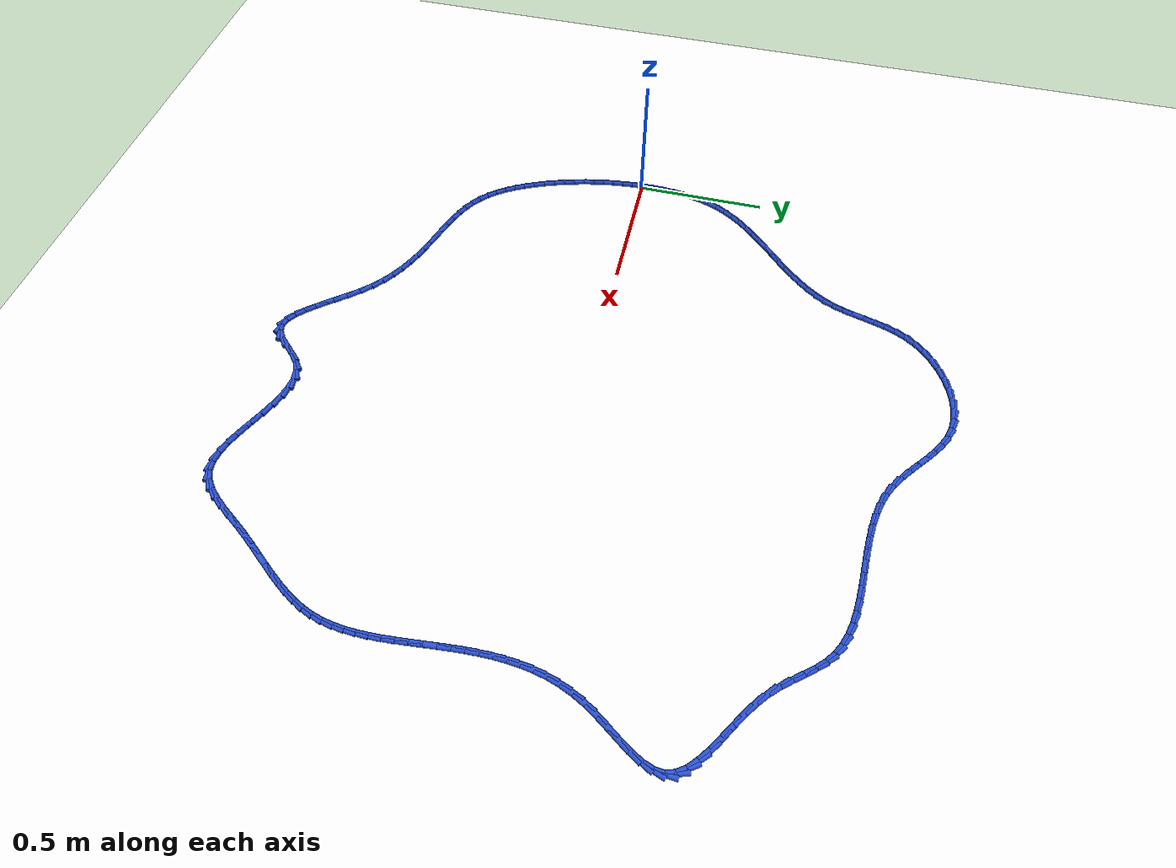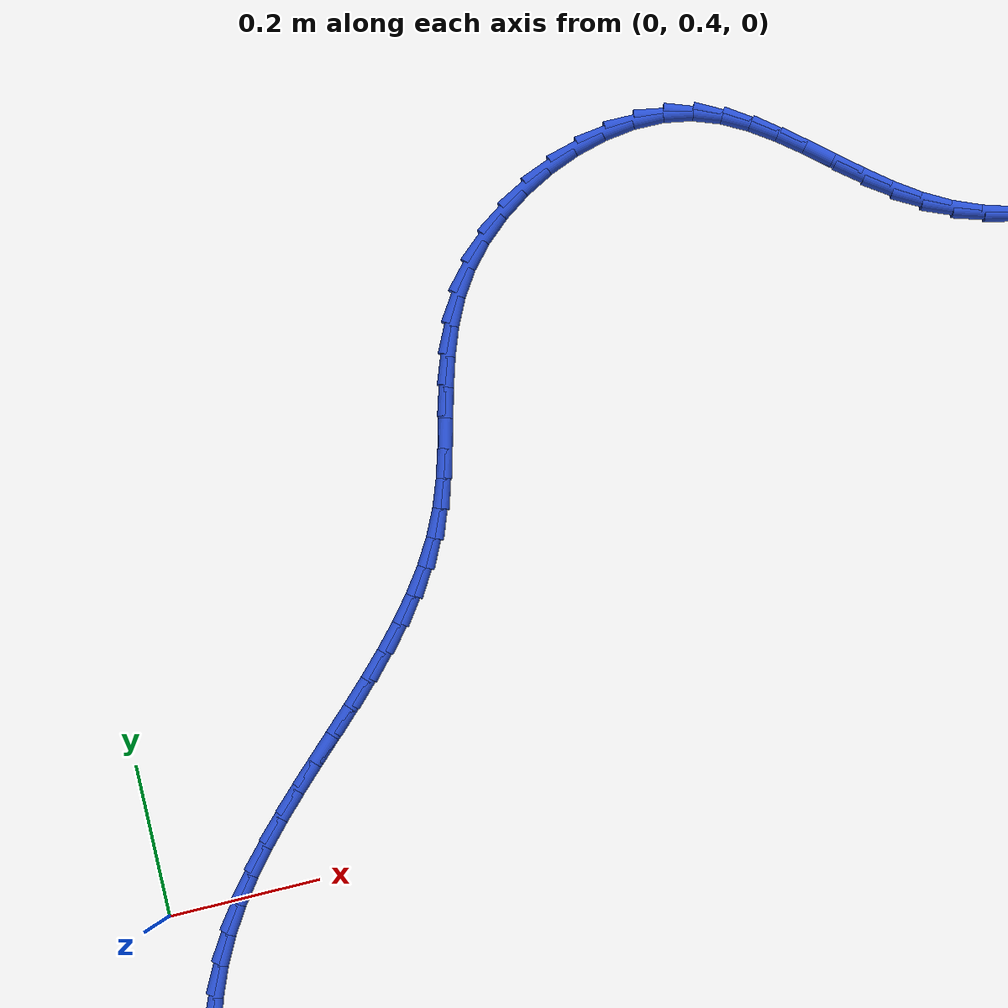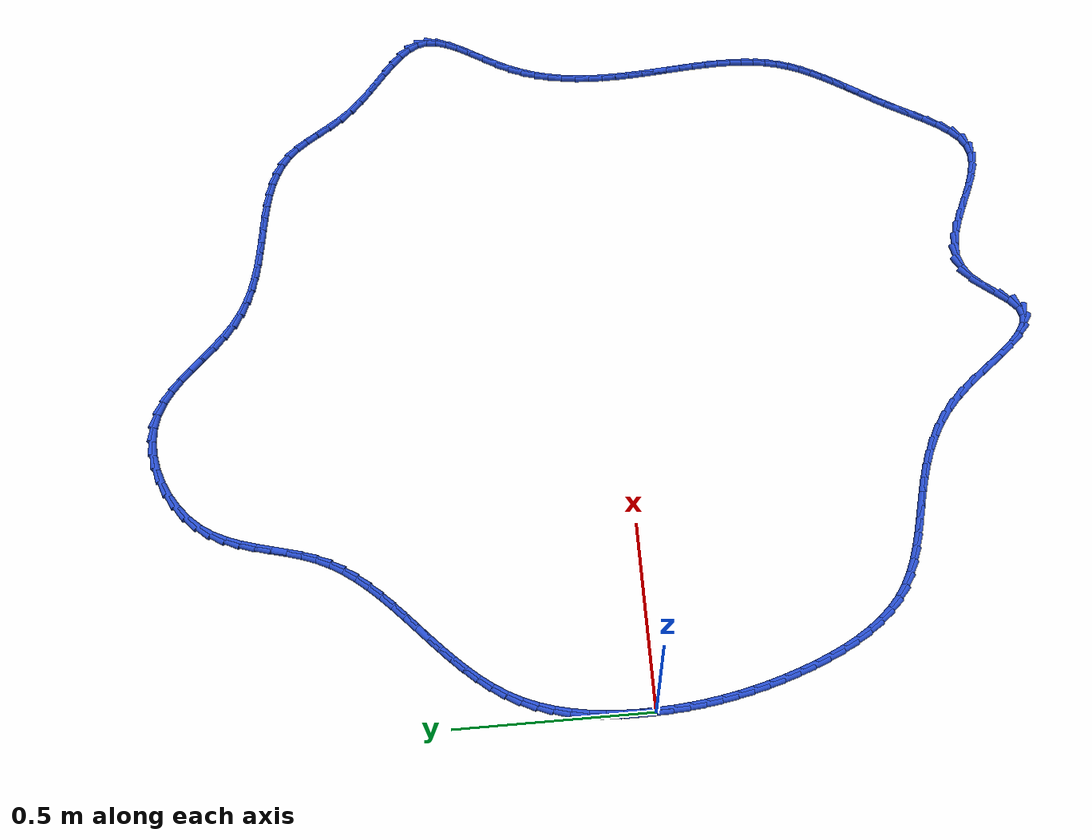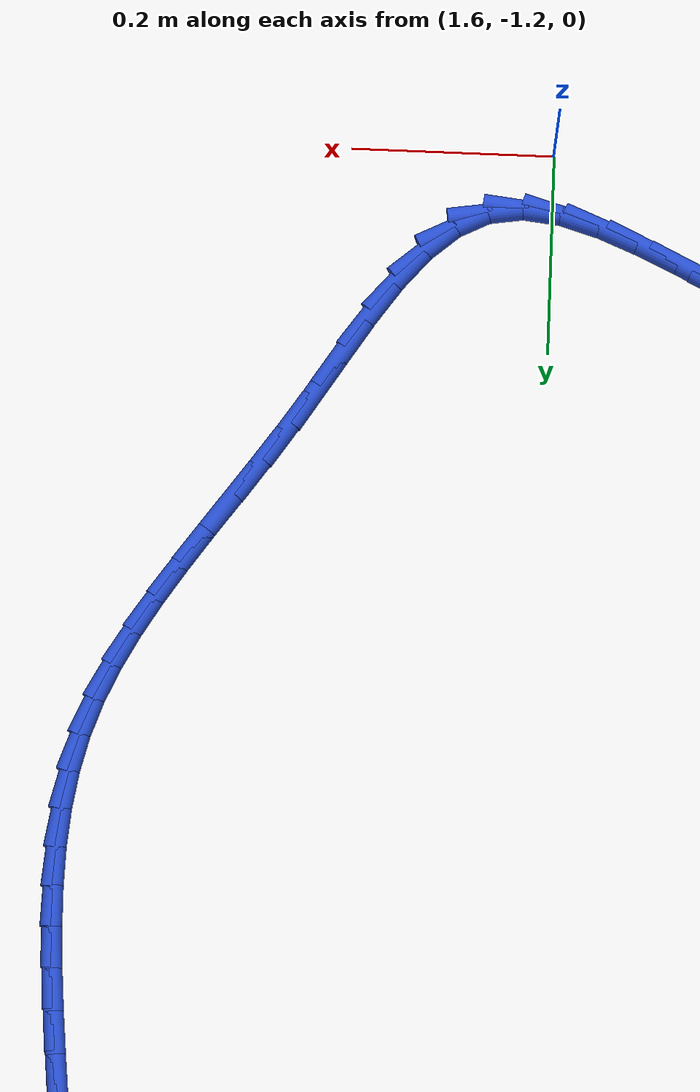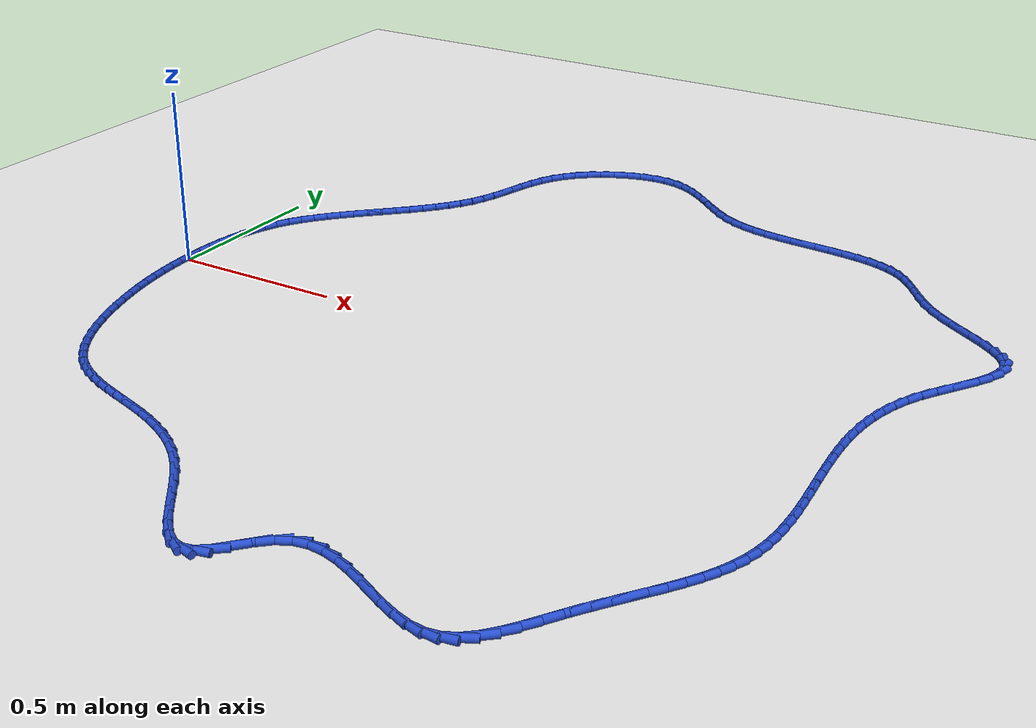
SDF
<sdf version="1.6">
 <world name="default">
  <light name="sun" type="directional">
   <pose>0 0 10 0 -0 0</pose>
   <diffuse>0.8 0.8 0.8 1</diffuse>
   <specular>0.2 0.2 0.2 1</specular>
   <attenuation>
    <range>1000</range>
    <constant>0.9</constant>
    <linear>0.01</linear>
    <quadratic>0.001</quadratic>
   </attenuation>
   <direction>-0.5 0.1 -0.9</direction>
  </light>
  <model name="ground_plane">
   <static>1</static>
   <link name="link">
    <collision name="collision">
     <geometry><plane><normal>0 0 1</normal><size>100 100</size></plane></geometry>
     <surface><friction><ode><mu>100</mu><mu2>50</mu2></ode></friction></surface>
    </collision>
    <visual name="visual">
     <cast_shadows>0</cast_shadows>
     <geometry><plane><normal>0 0 1</normal><size>100 100</size></plane></geometry>
     <material>
      <script><uri>file://media/materials/scripts/gazebo.material</uri><name>Gazebo/WhiteGlow</name></script>
     </material>
    </visual>
   </link>
  </model>
  <gravity>0 0 -9.8</gravity>
  <magnetic_field>6e-06 2.3e-05 -4.2e-05</magnetic_field>
  <atmosphere type="adiabatic"/>
  <physics name="default_physics" default="0" type="ode">
   <max_step_size>0.001</max_step_size>
   <real_time_factor>1</real_time_factor>
   <real_time_update_rate>1000</real_time_update_rate>
  </physics>
  <scene><ambient>0.4 0.4 0.4 1</ambient><background>0.7 0.7 0.7 1</background><shadows>1</shadows></scene>
  <spherical_coordinates>
   <surface_model>EARTH_WGS84</surface_model>
   <latitude_deg>0</latitude_deg>
   <longitude_deg>0</longitude_deg>
   <elevation>0</elevation>
   <heading_deg>0</heading_deg>
  </spherical_coordinates>
  <model name="line">
   <link name="link_0">
    <pose>-3.209238430557093e-17 1.1102230246251565e-16 0.01 0 1.57 -1.5560850111418287</pose>
    <collision name="collision">
     <geometry><cylinder><radius>0.01</radius><length>0.08</length></cylinder></geometry>
    </collision>
    <visual name="visual">
     <material>
      <script><name>Gazebo/Blue</name><uri>file://media/materials/scripts/gazebo.material</uri></script>
     </material>
     <geometry><cylinder><radius>0.01</radius><length>0.08</length></cylinder></geometry>
    </visual>
   </link>
   <link name="link_1">
    <pose>-0.0006134665959751895 0.04169731339794919 0.01 0 1.57 1.5482634742002266</pose>
    <collision name="collision">
     <geometry><cylinder><radius>0.01</radius><length>0.08</length></cylinder></geometry>
    </collision>
    <visual name="visual">
     <material>
      <script><name>Gazebo/Blue</name><uri>file://media/materials/scripts/gazebo.material</uri></script>
     </material>
     <geometry><cylinder><radius>0.01</radius><length>0.08</length></cylinder></geometry>
    </visual>
   </link>
   <link name="link_2">
    <pose>0.00033184914600642207 0.08364299002199375 0.01 0 1.57 1.5054730850666602</pose>
    <collision name="collision">
     <geometry><cylinder><radius>0.01</radius><length>0.08</length></cylinder></geometry>
    </collision>
    <visual name="visual">
     <material>
      <script><name>Gazebo/Blue</name><uri>file://media/materials/scripts/gazebo.material</uri></script>
     </material>
     <geometry><cylinder><radius>0.01</radius><length>0.08</length></cylinder></geometry>
    </visual>
   </link>
   <link name="link_3">
    <pose>0.003073877823221967 0.12555957745616575 0.01 0 1.57 1.4565005141774403</pose>
    <collision name="collision">
     <geometry><cylinder><radius>0.01</radius><length>0.08</length></cylinder></geometry>
    </collision>
    <visual name="visual">
     <material>
      <script><name>Gazebo/Blue</name><uri>file://media/materials/scripts/gazebo.material</uri></script>
     </material>
     <geometry><cylinder><radius>0.01</radius><length>0.08</length></cylinder></geometry>
    </visual>
   </link>
   <link name="link_4">
    <pose>0.007850550032948614 0.16716962328449717 0.01 0 1.57 1.4006342696999396</pose>
    <collision name="collision">
     <geometry><cylinder><radius>0.01</radius><length>0.08</length></cylinder></geometry>
    </collision>
    <visual name="visual">
     <material>
      <script><name>Gazebo/Blue</name><uri>file://media/materials/scripts/gazebo.material</uri></script>
     </material>
     <geometry><cylinder><radius>0.01</radius><length>0.08</length></cylinder></geometry>
    </visual>
   </link>
   <link name="link_5">
    <pose>0.014899796372463523 0.20819567509101997 0.01 0 1.57 1.33712972828409</pose>
    <collision name="collision">
     <geometry><cylinder><radius>0.01</radius><length>0.08</length></cylinder></geometry>
    </collision>
    <visual name="visual">
     <material>
      <script><name>Gazebo/Blue</name><uri>file://media/materials/scripts/gazebo.material</uri></script>
     </material>
     <geometry><cylinder><radius>0.01</radius><length>0.08</length></cylinder></geometry>
    </visual>
   </link>
   <link name="link_6">
    <pose>0.02445954743904385 0.24836028045976608 0.01 0 1.57 1.2652838038453469</pose>
    <collision name="collision">
     <geometry><cylinder><radius>0.01</radius><length>0.08</length></cylinder></geometry>
    </collision>
    <visual name="visual">
     <material>
      <script><name>Gazebo/Blue</name><uri>file://media/materials/scripts/gazebo.material</uri></script>
     </material>
     <geometry><cylinder><radius>0.01</radius><length>0.08</length></cylinder></geometry>
    </visual>
   </link>
   <link name="link_7">
    <pose>0.03676773382996677 0.2873859869747674 0.01 0 1.57 1.1845542153875608</pose>
    <collision name="collision">
     <geometry><cylinder><radius>0.01</radius><length>0.08</length></cylinder></geometry>
    </collision>
    <visual name="visual">
     <material>
      <script><name>Gazebo/Blue</name><uri>file://media/materials/scripts/gazebo.material</uri></script>
     </material>
     <geometry><cylinder><radius>0.01</radius><length>0.08</length></cylinder></geometry>
    </visual>
   </link>
   <link name="link_8">
    <pose>0.05206228614250945 0.32499534222005594 0.01 0 1.57 1.095259763297356</pose>
    <collision name="collision">
     <geometry><cylinder><radius>0.01</radius><length>0.08</length></cylinder></geometry>
    </collision>
    <visual name="visual">
     <material>
      <script><name>Gazebo/Blue</name><uri>file://media/materials/scripts/gazebo.material</uri></script>
     </material>
     <geometry><cylinder><radius>0.01</radius><length>0.08</length></cylinder></geometry>
    </visual>
   </link>
   <link name="link_9">
    <pose>0.07056377270829704 0.36092399320830526 0.01 0 1.57 1.0083837204269441</pose>
    <collision name="collision">
     <geometry><cylinder><radius>0.01</radius><length>0.08</length></cylinder></geometry>
    </collision>
    <visual name="visual">
     <material>
      <script><name>Gazebo/Blue</name><uri>file://media/materials/scripts/gazebo.material</uri></script>
     </material>
     <geometry><cylinder><radius>0.01</radius><length>0.08</length></cylinder></geometry>
    </visual>
   </link>
   <link name="link_10">
    <pose>0.09214807780678616 0.39516764311281943 0.01 0 1.57 0.9345323404183119</pose>
    <collision name="collision">
     <geometry><cylinder><radius>0.01</radius><length>0.08</length></cylinder></geometry>
    </collision>
    <visual name="visual">
     <material>
      <script><name>Gazebo/Blue</name><uri>file://media/materials/scripts/gazebo.material</uri></script>
     </material>
     <geometry><cylinder><radius>0.01</radius><length>0.08</length></cylinder></geometry>
    </visual>
   </link>
   <link name="link_11">
    <pose>0.11637427786301774 0.4279610193198251 0.01 0 1.57 0.8743204340232672</pose>
    <collision name="collision">
     <geometry><cylinder><radius>0.01</radius><length>0.08</length></cylinder></geometry>
    </collision>
    <visual name="visual">
     <material>
      <script><name>Gazebo/Blue</name><uri>file://media/materials/scripts/gazebo.material</uri></script>
     </material>
     <geometry><cylinder><radius>0.01</radius><length>0.08</length></cylinder></geometry>
    </visual>
   </link>
   <link name="link_12">
    <pose>0.14278967470873452 0.45954773287438694 0.01 0 1.57 0.8274277241909768</pose>
    <collision name="collision">
     <geometry><cylinder><radius>0.01</radius><length>0.08</length></cylinder></geometry>
    </collision>
    <visual name="visual">
     <material>
      <script><name>Gazebo/Blue</name><uri>file://media/materials/scripts/gazebo.material</uri></script>
     </material>
     <geometry><cylinder><radius>0.01</radius><length>0.08</length></cylinder></geometry>
    </visual>
   </link>
   <link name="link_13">
    <pose>0.17094157017567937 0.4901713948215696 0.01 0 1.57 0.7932936197868176</pose>
    <collision name="collision">
     <geometry><cylinder><radius>0.01</radius><length>0.08</length></cylinder></geometry>
    </collision>
    <visual name="visual">
     <material>
      <script><name>Gazebo/Blue</name><uri>file://media/materials/scripts/gazebo.material</uri></script>
     </material>
     <geometry><cylinder><radius>0.01</radius><length>0.08</length></cylinder></geometry>
    </visual>
   </link>
   <link name="link_14">
    <pose>0.20037726609559484 0.5200756162064372 0.01 0 1.57 0.7713542979603596</pose>
    <collision name="collision">
     <geometry><cylinder><radius>0.01</radius><length>0.08</length></cylinder></geometry>
    </collision>
    <visual name="visual">
     <material>
      <script><name>Gazebo/Blue</name><uri>file://media/materials/scripts/gazebo.material</uri></script>
     </material>
     <geometry><cylinder><radius>0.01</radius><length>0.08</length></cylinder></geometry>
    </visual>
   </link>
   <link name="link_15">
    <pose>0.2306440643002238 0.5495040080740543 0.01 0 1.57 0.761188395505557</pose>
    <collision name="collision">
     <geometry><cylinder><radius>0.01</radius><length>0.08</length></cylinder></geometry>
    </collision>
    <visual name="visual">
     <material>
      <script><name>Gazebo/Blue</name><uri>file://media/materials/scripts/gazebo.material</uri></script>
     </material>
     <geometry><cylinder><radius>0.01</radius><length>0.08</length></cylinder></geometry>
    </visual>
   </link>
   <link name="link_16">
    <pose>0.26128926662130886 0.5787001814694853 0.01 0 1.57 0.7625955406162549</pose>
    <collision name="collision">
     <geometry><cylinder><radius>0.01</radius><length>0.08</length></cylinder></geometry>
    </collision>
    <visual name="visual">
     <material>
      <script><name>Gazebo/Blue</name><uri>file://media/materials/scripts/gazebo.material</uri></script>
     </material>
     <geometry><cylinder><radius>0.01</radius><length>0.08</length></cylinder></geometry>
    </visual>
   </link>
   <link name="link_17">
    <pose>0.2918601748905928 0.6079077474377944 0.01 0 1.57 0.7756290102910977</pose>
    <collision name="collision">
     <geometry><cylinder><radius>0.01</radius><length>0.08</length></cylinder></geometry>
    </collision>
    <visual name="visual">
     <material>
      <script><name>Gazebo/Blue</name><uri>file://media/materials/scripts/gazebo.material</uri></script>
     </material>
     <geometry><cylinder><radius>0.01</radius><length>0.08</length></cylinder></geometry>
    </visual>
   </link>
   <link name="link_18">
    <pose>0.3219040909398184 0.6373703170240466 0.01 0 1.57 0.8005931371648121</pose>
    <collision name="collision">
     <geometry><cylinder><radius>0.01</radius><length>0.08</length></cylinder></geometry>
    </collision>
    <visual name="visual">
     <material>
      <script><name>Gazebo/Blue</name><uri>file://media/materials/scripts/gazebo.material</uri></script>
     </material>
     <geometry><cylinder><radius>0.01</radius><length>0.08</length></cylinder></geometry>
    </visual>
   </link>
   <link name="link_19">
    <pose>0.35096831660072825 0.6673315012733059 0.01 0 1.57 0.8380033918524153</pose>
    <collision name="collision">
     <geometry><cylinder><radius>0.01</radius><length>0.08</length></cylinder></geometry>
    </collision>
    <visual name="visual">
     <material>
      <script><name>Gazebo/Blue</name><uri>file://media/materials/scripts/gazebo.material</uri></script>
     </material>
     <geometry><cylinder><radius>0.01</radius><length>0.08</length></cylinder></geometry>
    </visual>
   </link>
   <link name="link_20">
    <pose>0.3786001537050653 0.6980349112306367 0.01 0 1.57 0.8884942671636429</pose>
    <collision name="collision">
     <geometry><cylinder><radius>0.01</radius><length>0.08</length></cylinder></geometry>
    </collision>
    <visual name="visual">
     <material>
      <script><name>Gazebo/Blue</name><uri>file://media/materials/scripts/gazebo.material</uri></script>
     </material>
     <geometry><cylinder><radius>0.01</radius><length>0.08</length></cylinder></geometry>
    </visual>
   </link>
   <link name="link_21">
    <pose>0.4043469040845722 0.7297241579411039 0.01 0 1.57 0.9526497593310148</pose>
    <collision name="collision">
     <geometry><cylinder><radius>0.01</radius><length>0.08</length></cylinder></geometry>
    </collision>
    <visual name="visual">
     <material>
      <script><name>Gazebo/Blue</name><uri>file://media/materials/scripts/gazebo.material</uri></script>
     </material>
     <geometry><cylinder><radius>0.01</radius><length>0.08</length></cylinder></geometry>
    </visual>
   </link>
   <link name="link_22">
    <pose>0.4277558695709916 0.7626428524497715 0.01 0 1.57 1.0307311588188617</pose>
    <collision name="collision">
     <geometry><cylinder><radius>0.01</radius><length>0.08</length></cylinder></geometry>
    </collision>
    <visual name="visual">
     <material>
      <script><name>Gazebo/Blue</name><uri>file://media/materials/scripts/gazebo.material</uri></script>
     </material>
     <geometry><cylinder><radius>0.01</radius><length>0.08</length></cylinder></geometry>
    </visual>
   </link>
   <link name="link_23">
    <pose>0.4483743519960662 0.7970346058017039 0.01 0 1.57 1.1222995798715842</pose>
    <collision name="collision">
     <geometry><cylinder><radius>0.01</radius><length>0.08</length></cylinder></geometry>
    </collision>
    <visual name="visual">
     <material>
      <script><name>Gazebo/Blue</name><uri>file://media/materials/scripts/gazebo.material</uri></script>
     </material>
     <geometry><cylinder><radius>0.01</radius><length>0.08</length></cylinder></geometry>
    </visual>
   </link>
   <link name="link_24">
    <pose>0.4657497809316493 0.833142965838233 0.01 0 1.57 1.216325336079126</pose>
    <collision name="collision">
     <geometry><cylinder><radius>0.01</radius><length>0.08</length></cylinder></geometry>
    </collision>
    <visual name="visual">
     <material>
      <script><name>Gazebo/Blue</name><uri>file://media/materials/scripts/gazebo.material</uri></script>
     </material>
     <geometry><cylinder><radius>0.01</radius><length>0.08</length></cylinder></geometry>
    </visual>
   </link>
   <link name="link_25">
    <pose>0.47977569341693094 0.8710402320460279 0.01 0 1.57 1.2815588687121973</pose>
    <collision name="collision">
     <geometry><cylinder><radius>0.01</radius><length>0.08</length></cylinder></geometry>
    </collision>
    <visual name="visual">
     <material>
      <script><name>Gazebo/Blue</name><uri>file://media/materials/scripts/gazebo.material</uri></script>
     </material>
     <geometry><cylinder><radius>0.01</radius><length>0.08</length></cylinder></geometry>
    </visual>
   </link>
   <link name="link_26">
    <pose>0.4914452173575355 0.910254644206461 0.01 0 1.57 1.313227993498288</pose>
    <collision name="collision">
     <geometry><cylinder><radius>0.01</radius><length>0.08</length></cylinder></geometry>
    </collision>
    <visual name="visual">
     <material>
      <script><name>Gazebo/Blue</name><uri>file://media/materials/scripts/gazebo.material</uri></script>
     </material>
     <geometry><cylinder><radius>0.01</radius><length>0.08</length></cylinder></geometry>
    </visual>
   </link>
   <link name="link_27">
    <pose>0.5019693517239366 0.9502066430358587 0.01 0 1.57 1.3126689691735742</pose>
    <collision name="collision">
     <geometry><cylinder><radius>0.01</radius><length>0.08</length></cylinder></geometry>
    </collision>
    <visual name="visual">
     <material>
      <script><name>Gazebo/Blue</name><uri>file://media/materials/scripts/gazebo.material</uri></script>
     </material>
     <geometry><cylinder><radius>0.01</radius><length>0.08</length></cylinder></geometry>
    </visual>
   </link>
   <link name="link_28">
    <pose>0.5125590954866084 0.990316669250548 0.01 0 1.57 1.2802689575430162</pose>
    <collision name="collision">
     <geometry><cylinder><radius>0.01</radius><length>0.08</length></cylinder></geometry>
    </collision>
    <visual name="visual">
     <material>
      <script><name>Gazebo/Blue</name><uri>file://media/materials/scripts/gazebo.material</uri></script>
     </material>
     <geometry><cylinder><radius>0.01</radius><length>0.08</length></cylinder></geometry>
    </visual>
   </link>
   <link name="link_29">
    <pose>0.5244254476160246 1.0300051635668557 0.01 0 1.57 1.2155159129956474</pose>
    <collision name="collision">
     <geometry><cylinder><radius>0.01</radius><length>0.08</length></cylinder></geometry>
    </collision>
    <visual name="visual">
     <material>
      <script><name>Gazebo/Blue</name><uri>file://media/materials/scripts/gazebo.material</uri></script>
     </material>
     <geometry><cylinder><radius>0.01</radius><length>0.08</length></cylinder></geometry>
    </visual>
   </link>
   <link name="link_30">
    <pose>0.5387794070826591 1.0686925667011087 0.01 0 1.57 1.118004081680076</pose>
    <collision name="collision">
     <geometry><cylinder><radius>0.01</radius><length>0.08</length></cylinder></geometry>
    </collision>
    <visual name="visual">
     <material>
      <script><name>Gazebo/Blue</name><uri>file://media/materials/scripts/gazebo.material</uri></script>
     </material>
     <geometry><cylinder><radius>0.01</radius><length>0.08</length></cylinder></geometry>
    </visual>
   </link>
   <link name="link_31">
    <pose>0.5568319728569857 1.1057993193696338 0.01 0 1.57 0.9895973113790022</pose>
    <collision name="collision">
     <geometry><cylinder><radius>0.01</radius><length>0.08</length></cylinder></geometry>
    </collision>
    <visual name="visual">
     <material>
      <script><name>Gazebo/Blue</name><uri>file://media/materials/scripts/gazebo.material</uri></script>
     </material>
     <geometry><cylinder><radius>0.01</radius><length>0.08</length></cylinder></geometry>
    </visual>
   </link>
   <link name="link_32">
    <pose>0.579787966241789 1.1407461462083541 0.01 0 1.57 0.8490300604744137</pose>
    <collision name="collision">
     <geometry><cylinder><radius>0.01</radius><length>0.08</length></cylinder></geometry>
    </collision>
    <visual name="visual">
     <material>
      <script><name>Gazebo/Blue</name><uri>file://media/materials/scripts/gazebo.material</uri></script>
     </material>
     <geometry><cylinder><radius>0.01</radius><length>0.08</length></cylinder></geometry>
    </visual>
   </link>
   <link name="link_33">
    <pose>0.608164850456559 1.1729853621619197 0.01 0 1.57 0.7215480919830476</pose>
    <collision name="collision">
     <geometry><cylinder><radius>0.01</radius><length>0.08</length></cylinder></geometry>
    </collision>
    <visual name="visual">
     <material>
      <script><name>Gazebo/Blue</name><uri>file://media/materials/scripts/gazebo.material</uri></script>
     </material>
     <geometry><cylinder><radius>0.01</radius><length>0.08</length></cylinder></geometry>
    </visual>
   </link>
   <link name="link_34">
    <pose>0.6411763195999719 1.2020292021352388 0.01 0 1.57 0.6046207540081676</pose>
    <collision name="collision">
     <geometry><cylinder><radius>0.01</radius><length>0.08</length></cylinder></geometry>
    </collision>
    <visual name="visual">
     <material>
      <script><name>Gazebo/Blue</name><uri>file://media/materials/scripts/gazebo.material</uri></script>
     </material>
     <geometry><cylinder><radius>0.01</radius><length>0.08</length></cylinder></geometry>
    </visual>
   </link>
   <link name="link_35">
    <pose>0.6778905350938581 1.22739658957345 0.01 0 1.57 0.49293241044690883</pose>
    <collision name="collision">
     <geometry><cylinder><radius>0.01</radius><length>0.08</length></cylinder></geometry>
    </collision>
    <visual name="visual">
     <material>
      <script><name>Gazebo/Blue</name><uri>file://media/materials/scripts/gazebo.material</uri></script>
     </material>
     <geometry><cylinder><radius>0.01</radius><length>0.08</length></cylinder></geometry>
    </visual>
   </link>
   <link name="link_36">
    <pose>0.717375658360046 1.2486064479216898 0.01 0 1.57 0.38137339220141653</pose>
    <collision name="collision">
     <geometry><cylinder><radius>0.01</radius><length>0.08</length></cylinder></geometry>
    </collision>
    <visual name="visual">
     <material>
      <script><name>Gazebo/Blue</name><uri>file://media/materials/scripts/gazebo.material</uri></script>
     </material>
     <geometry><cylinder><radius>0.01</radius><length>0.08</length></cylinder></geometry>
    </visual>
   </link>
   <link name="link_37">
    <pose>0.7586998508203648 1.2651777006250964 0.01 0 1.57 0.26479485804835917</pose>
    <collision name="collision">
     <geometry><cylinder><radius>0.01</radius><length>0.08</length></cylinder></geometry>
    </collision>
    <visual name="visual">
     <material>
      <script><name>Gazebo/Blue</name><uri>file://media/materials/scripts/gazebo.material</uri></script>
     </material>
     <geometry><cylinder><radius>0.01</radius><length>0.08</length></cylinder></geometry>
    </visual>
   </link>
   <link name="link_38">
    <pose>0.8009312738966439 1.2766292711288068 0.01 0 1.57 0.13774460908547448</pose>
    <collision name="collision">
     <geometry><cylinder><radius>0.01</radius><length>0.08</length></cylinder></geometry>
    </collision>
    <visual name="visual">
     <material>
      <script><name>Gazebo/Blue</name><uri>file://media/materials/scripts/gazebo.material</uri></script>
     </material>
     <geometry><cylinder><radius>0.01</radius><length>0.08</length></cylinder></geometry>
    </visual>
   </link>
   <link name="link_39">
    <pose>0.8431380890107123 1.2824800828779594 0.01 0 1.57 -0.005600462562805353</pose>
    <collision name="collision">
     <geometry><cylinder><radius>0.01</radius><length>0.08</length></cylinder></geometry>
    </collision>
    <visual name="visual">
     <material>
      <script><name>Gazebo/Blue</name><uri>file://media/materials/scripts/gazebo.material</uri></script>
     </material>
     <geometry><cylinder><radius>0.01</radius><length>0.08</length></cylinder></geometry>
    </visual>
   </link>
   <link name="link_40">
    <pose>0.8843884575843992 1.2822490593176903 0.01 0 1.57 -0.17090499398291586</pose>
    <collision name="collision">
     <geometry><cylinder><radius>0.01</radius><length>0.08</length></cylinder></geometry>
    </collision>
    <visual name="visual">
     <material>
      <script><name>Gazebo/Blue</name><uri>file://media/materials/scripts/gazebo.material</uri></script>
     </material>
     <geometry><cylinder><radius>0.01</radius><length>0.08</length></cylinder></geometry>
    </visual>
   </link>
   <link name="link_41">
    <pose>0.923750896451844 1.2754555500077551 0.01 0 1.57 -0.3490179393192631</pose>
    <collision name="collision">
     <geometry><cylinder><radius>0.01</radius><length>0.08</length></cylinder></geometry>
    </collision>
    <visual name="visual">
     <material>
      <script><name>Gazebo/Blue</name><uri>file://media/materials/scripts/gazebo.material</uri></script>
     </material>
     <geometry><cylinder><radius>0.01</radius><length>0.08</length></cylinder></geometry>
    </visual>
   </link>
   <link name="link_42">
    <pose>0.9606382010026505 1.2620316705279229 0.01 0 1.57 -0.498248297932133</pose>
    <collision name="collision">
     <geometry><cylinder><radius>0.01</radius><length>0.08</length></cylinder></geometry>
    </collision>
    <visual name="visual">
     <material>
      <script><name>Gazebo/Blue</name><uri>file://media/materials/scripts/gazebo.material</uri></script>
     </material>
     <geometry><cylinder><radius>0.01</radius><length>0.08</length></cylinder></geometry>
    </visual>
   </link>
   <link name="link_43">
    <pose>0.9954501839415857 1.243092901504668 0.01 0 1.57 -0.6068649200676309</pose>
    <collision name="collision">
     <geometry><cylinder><radius>0.01</radius><length>0.08</length></cylinder></geometry>
    </collision>
    <visual name="visual">
     <material>
      <script><name>Gazebo/Blue</name><uri>file://media/materials/scripts/gazebo.material</uri></script>
     </material>
     <geometry><cylinder><radius>0.01</radius><length>0.08</length></cylinder></geometry>
    </visual>
   </link>
   <link name="link_44">
    <pose>1.0287624276467986 1.219965459166115 0.01 0 1.57 -0.6762345465372139</pose>
    <collision name="collision">
     <geometry><cylinder><radius>0.01</radius><length>0.08</length></cylinder></geometry>
    </collision>
    <visual name="visual">
     <material>
      <script><name>Gazebo/Blue</name><uri>file://media/materials/scripts/gazebo.material</uri></script>
     </material>
     <geometry><cylinder><radius>0.01</radius><length>0.08</length></cylinder></geometry>
    </visual>
   </link>
   <link name="link_45">
    <pose>1.0611505144964404 1.1939755597403912 0.01 0 1.57 -0.7097712882787738</pose>
    <collision name="collision">
     <geometry><cylinder><radius>0.01</radius><length>0.08</length></cylinder></geometry>
    </collision>
    <visual name="visual">
     <material>
      <script><name>Gazebo/Blue</name><uri>file://media/materials/scripts/gazebo.material</uri></script>
     </material>
     <geometry><cylinder><radius>0.01</radius><length>0.08</length></cylinder></geometry>
    </visual>
   </link>
   <link name="link_46">
    <pose>1.0931900268686603 1.1664494194556212 0.01 0 1.57 -0.7100386018089009</pose>
    <collision name="collision">
     <geometry><cylinder><radius>0.01</radius><length>0.08</length></cylinder></geometry>
    </collision>
    <visual name="visual">
     <material>
      <script><name>Gazebo/Blue</name><uri>file://media/materials/scripts/gazebo.material</uri></script>
     </material>
     <geometry><cylinder><radius>0.01</radius><length>0.08</length></cylinder></geometry>
    </visual>
   </link>
   <link name="link_47">
    <pose>1.1254565471416085 1.1387132545399319 0.01 0 1.57 -0.6777701724831824</pose>
    <collision name="collision">
     <geometry><cylinder><radius>0.01</radius><length>0.08</length></cylinder></geometry>
    </collision>
    <visual name="visual">
     <material>
      <script><name>Gazebo/Blue</name><uri>file://media/materials/scripts/gazebo.material</uri></script>
     </material>
     <geometry><cylinder><radius>0.01</radius><length>0.08</length></cylinder></geometry>
    </visual>
   </link>
   <link name="link_48">
    <pose>1.1585256576934349 1.1120932812214492 0.01 0 1.57 -0.6119808842164338</pose>
    <collision name="collision">
     <geometry><cylinder><radius>0.01</radius><length>0.08</length></cylinder></geometry>
    </collision>
    <visual name="visual">
     <material>
      <script><name>Gazebo/Blue</name><uri>file://media/materials/scripts/gazebo.material</uri></script>
     </material>
     <geometry><cylinder><radius>0.01</radius><length>0.08</length></cylinder></geometry>
    </visual>
   </link>
   <link name="link_49">
    <pose>1.1929729409022902 1.0879157157282981 0.01 0 1.57 -0.5112355242063512</pose>
    <collision name="collision">
     <geometry><cylinder><radius>0.01</radius><length>0.08</length></cylinder></geometry>
    </collision>
    <visual name="visual">
     <material>
      <script><name>Gazebo/Blue</name><uri>file://media/materials/scripts/gazebo.material</uri></script>
     </material>
     <geometry><cylinder><radius>0.01</radius><length>0.08</length></cylinder></geometry>
    </visual>
   </link>
   <link name="link_50">
    <pose>1.2293696374610912 1.0674978264292825 0.01 0 1.57 -0.39395526314767665</pose>
    <collision name="collision">
     <geometry><cylinder><radius>0.01</radius><length>0.08</length></cylinder></geometry>
    </collision>
    <visual name="visual">
     <material>
      <script><name>Gazebo/Blue</name><uri>file://media/materials/scripts/gazebo.material</uri></script>
     </material>
     <geometry><cylinder><radius>0.01</radius><length>0.08</length></cylinder></geometry>
    </visual>
   </link>
   <link name="link_51">
    <pose>1.2679492455942383 1.0514608219988621 0.01 0 1.57 -0.2935019336537761</pose>
    <collision name="collision">
     <geometry><cylinder><radius>0.01</radius><length>0.08</length></cylinder></geometry>
    </collision>
    <visual name="visual">
     <material>
      <script><name>Gazebo/Blue</name><uri>file://media/materials/scripts/gazebo.material</uri></script>
     </material>
     <geometry><cylinder><radius>0.01</radius><length>0.08</length></cylinder></geometry>
    </visual>
   </link>
   <link name="link_52">
    <pose>1.3083717325773891 1.039243910581247 0.01 0 1.57 -0.2133826975024367</pose>
    <collision name="collision">
     <geometry><cylinder><radius>0.01</radius><length>0.08</length></cylinder></geometry>
    </collision>
    <visual name="visual">
     <material>
      <script><name>Gazebo/Blue</name><uri>file://media/materials/scripts/gazebo.material</uri></script>
     </material>
     <geometry><cylinder><radius>0.01</radius><length>0.08</length></cylinder></geometry>
    </visual>
   </link>
   <link name="link_53">
    <pose>1.3502413803766289 1.0301715374371643 0.01 0 1.57 -0.15265262641293062</pose>
    <collision name="collision">
     <geometry><cylinder><radius>0.01</radius><length>0.08</length></cylinder></geometry>
    </collision>
    <visual name="visual">
     <material>
      <script><name>Gazebo/Blue</name><uri>file://media/materials/scripts/gazebo.material</uri></script>
     </material>
     <geometry><cylinder><radius>0.01</radius><length>0.08</length></cylinder></geometry>
    </visual>
   </link>
   <link name="link_54">
    <pose>1.3931624709580412 1.0235681478273404 0.01 0 1.57 -0.10993387858803776</pose>
    <collision name="collision">
     <geometry><cylinder><radius>0.01</radius><length>0.08</length></cylinder></geometry>
    </collision>
    <visual name="visual">
     <material>
      <script><name>Gazebo/Blue</name><uri>file://media/materials/scripts/gazebo.material</uri></script>
     </material>
     <geometry><cylinder><radius>0.01</radius><length>0.08</length></cylinder></geometry>
    </visual>
   </link>
   <link name="link_55">
    <pose>1.4367392862877113 1.018758187012503 0.01 0 1.57 -0.08402510754415692</pose>
    <collision name="collision">
     <geometry><cylinder><radius>0.01</radius><length>0.08</length></cylinder></geometry>
    </collision>
    <visual name="visual">
     <material>
      <script><name>Gazebo/Blue</name><uri>file://media/materials/scripts/gazebo.material</uri></script>
     </material>
     <geometry><cylinder><radius>0.01</radius><length>0.08</length></cylinder></geometry>
    </visual>
   </link>
   <link name="link_56">
    <pose>1.4805761083317222 1.015066100253379 0.01 0 1.57 -0.074226875651785</pose>
    <collision name="collision">
     <geometry><cylinder><radius>0.01</radius><length>0.08</length></cylinder></geometry>
    </collision>
    <visual name="visual">
     <material>
      <script><name>Gazebo/Blue</name><uri>file://media/materials/scripts/gazebo.material</uri></script>
     </material>
     <geometry><cylinder><radius>0.01</radius><length>0.08</length></cylinder></geometry>
    </visual>
   </link>
   <link name="link_57">
    <pose>1.524277219056159 1.0118163328106953 0.01 0 1.57 -0.08050730419673535</pose>
    <collision name="collision">
     <geometry><cylinder><radius>0.01</radius><length>0.08</length></cylinder></geometry>
    </collision>
    <visual name="visual">
     <material>
      <script><name>Gazebo/Blue</name><uri>file://media/materials/scripts/gazebo.material</uri></script>
     </material>
     <geometry><cylinder><radius>0.01</radius><length>0.08</length></cylinder></geometry>
    </visual>
   </link>
   <link name="link_58">
    <pose>1.567446900427106 1.008333329945179 0.01 0 1.57 -0.1035939581052474</pose>
    <collision name="collision">
     <geometry><cylinder><radius>0.01</radius><length>0.08</length></cylinder></geometry>
    </collision>
    <visual name="visual">
     <material>
      <script><name>Gazebo/Blue</name><uri>file://media/materials/scripts/gazebo.material</uri></script>
     </material>
     <geometry><cylinder><radius>0.01</radius><length>0.08</length></cylinder></geometry>
    </visual>
   </link>
   <link name="link_59">
    <pose>1.6096894344106472 1.0039415369175577 0.01 0 1.57 -0.14502034740108105</pose>
    <collision name="collision">
     <geometry><cylinder><radius>0.01</radius><length>0.08</length></cylinder></geometry>
    </collision>
    <visual name="visual">
     <material>
      <script><name>Gazebo/Blue</name><uri>file://media/materials/scripts/gazebo.material</uri></script>
     </material>
     <geometry><cylinder><radius>0.01</radius><length>0.08</length></cylinder></geometry>
    </visual>
   </link>
   <link name="link_60">
    <pose>1.650609102972867 0.9979653989885575 0.01 0 1.57 -0.20708527109241273</pose>
    <collision name="collision">
     <geometry><cylinder><radius>0.01</radius><length>0.08</length></cylinder></geometry>
    </collision>
    <visual name="visual">
     <material>
      <script><name>Gazebo/Blue</name><uri>file://media/materials/scripts/gazebo.material</uri></script>
     </material>
     <geometry><cylinder><radius>0.01</radius><length>0.08</length></cylinder></geometry>
    </visual>
   </link>
   <link name="link_61">
    <pose>1.6898101880798495 0.9897293614189061 0.01 0 1.57 -0.2925809001503532</pose>
    <collision name="collision">
     <geometry><cylinder><radius>0.01</radius><length>0.08</length></cylinder></geometry>
    </collision>
    <visual name="visual">
     <material>
      <script><name>Gazebo/Blue</name><uri>file://media/materials/scripts/gazebo.material</uri></script>
     </material>
     <geometry><cylinder><radius>0.01</radius><length>0.08</length></cylinder></geometry>
    </visual>
   </link>
   <link name="link_62">
    <pose>1.7268969716976788 0.9785578694693304 0.01 0 1.57 -0.4040091113266492</pose>
    <collision name="collision">
     <geometry><cylinder><radius>0.01</radius><length>0.08</length></cylinder></geometry>
    </collision>
    <visual name="visual">
     <material>
      <script><name>Gazebo/Blue</name><uri>file://media/materials/scripts/gazebo.material</uri></script>
     </material>
     <geometry><cylinder><radius>0.01</radius><length>0.08</length></cylinder></geometry>
    </visual>
   </link>
   <link name="link_63">
    <pose>1.7614737357924395 0.9637753684005572 0.01 0 1.57 -0.5419607935183058</pose>
    <collision name="collision">
     <geometry><cylinder><radius>0.01</radius><length>0.08</length></cylinder></geometry>
    </collision>
    <visual name="visual">
     <material>
      <script><name>Gazebo/Blue</name><uri>file://media/materials/scripts/gazebo.material</uri></script>
     </material>
     <geometry><cylinder><radius>0.01</radius><length>0.08</length></cylinder></geometry>
    </visual>
   </link>
   <link name="link_64">
    <pose>1.7931447623302161 0.9447063034733141 0.01 0 1.57 -0.6995481345048974</pose>
    <collision name="collision">
     <geometry><cylinder><radius>0.01</radius><length>0.08</length></cylinder></geometry>
    </collision>
    <visual name="visual">
     <material>
      <script><name>Gazebo/Blue</name><uri>file://media/materials/scripts/gazebo.material</uri></script>
     </material>
     <geometry><cylinder><radius>0.01</radius><length>0.08</length></cylinder></geometry>
    </visual>
   </link>
   <link name="link_65">
    <pose>1.82159616130616 0.9207639893849637 0.01 0 1.57 -0.8282231691425831</pose>
    <collision name="collision">
     <geometry><cylinder><radius>0.01</radius><length>0.08</length></cylinder></geometry>
    </collision>
    <visual name="visual">
     <material>
      <script><name>Gazebo/Blue</name><uri>file://media/materials/scripts/gazebo.material</uri></script>
     </material>
     <geometry><cylinder><radius>0.01</radius><length>0.08</length></cylinder></geometry>
    </visual>
   </link>
   <link name="link_66">
    <pose>1.8475497330316701 0.8924865536382546 0.01 0 1.57 -0.8990624771617428</pose>
    <collision name="collision">
     <geometry><cylinder><radius>0.01</radius><length>0.08</length></cylinder></geometry>
    </collision>
    <visual name="visual">
     <material>
      <script><name>Gazebo/Blue</name><uri>file://media/materials/scripts/gazebo.material</uri></script>
     </material>
     <geometry><cylinder><radius>0.01</radius><length>0.08</length></cylinder></geometry>
    </visual>
   </link>
   <link name="link_67">
    <pose>1.872437876429372 0.86118387027528 0.01 0 1.57 -0.9173484359255261</pose>
    <collision name="collision">
     <geometry><cylinder><radius>0.01</radius><length>0.08</length></cylinder></geometry>
    </collision>
    <visual name="visual">
     <material>
      <script><name>Gazebo/Blue</name><uri>file://media/materials/scripts/gazebo.material</uri></script>
     </material>
     <geometry><cylinder><radius>0.01</radius><length>0.08</length></cylinder></geometry>
    </visual>
   </link>
   <link name="link_68">
    <pose>1.897706893700599 0.8281809130119261 0.01 0 1.57 -0.8889065485625</pose>
    <collision name="collision">
     <geometry><cylinder><radius>0.01</radius><length>0.08</length></cylinder></geometry>
    </collision>
    <visual name="visual">
     <material>
      <script><name>Gazebo/Blue</name><uri>file://media/materials/scripts/gazebo.material</uri></script>
     </material>
     <geometry><cylinder><radius>0.01</radius><length>0.08</length></cylinder></geometry>
    </visual>
   </link>
   <link name="link_69">
    <pose>1.9248030870466841 0.7948026555640797 0.01 0 1.57 -0.8181725617067681</pose>
    <collision name="collision">
     <geometry><cylinder><radius>0.01</radius><length>0.08</length></cylinder></geometry>
    </collision>
    <visual name="visual">
     <material>
      <script><name>Gazebo/Blue</name><uri>file://media/materials/scripts/gazebo.material</uri></script>
     </material>
     <geometry><cylinder><radius>0.01</radius><length>0.08</length></cylinder></geometry>
    </visual>
   </link>
   <link name="link_70">
    <pose>1.9551727586689593 0.7623740716476279 0.01 0 1.57 -0.7189248837944462</pose>
    <collision name="collision">
     <geometry><cylinder><radius>0.01</radius><length>0.08</length></cylinder></geometry>
    </collision>
    <visual name="visual">
     <material>
      <script><name>Gazebo/Blue</name><uri>file://media/materials/scripts/gazebo.material</uri></script>
     </material>
     <geometry><cylinder><radius>0.01</radius><length>0.08</length></cylinder></geometry>
    </visual>
   </link>
   <link name="link_71">
    <pose>1.9898760083517668 0.7320029138616024 0.01 0 1.57 -0.643028336924543</pose>
    <collision name="collision">
     <geometry><cylinder><radius>0.01</radius><length>0.08</length></cylinder></geometry>
    </collision>
    <visual name="visual">
     <material>
      <script><name>Gazebo/Blue</name><uri>file://media/materials/scripts/gazebo.material</uri></script>
     </material>
     <geometry><cylinder><radius>0.01</radius><length>0.08</length></cylinder></geometry>
    </visual>
   </link>
   <link name="link_72">
    <pose>2.0278100377541124 0.7035804039762343 0.01 0 1.57 -0.6019525893170691</pose>
    <collision name="collision">
     <geometry><cylinder><radius>0.01</radius><length>0.08</length></cylinder></geometry>
    </collision>
    <visual name="visual">
     <material>
      <script><name>Gazebo/Blue</name><uri>file://media/materials/scripts/gazebo.material</uri></script>
     </material>
     <geometry><cylinder><radius>0.01</radius><length>0.08</length></cylinder></geometry>
    </visual>
   </link>
   <link name="link_73">
    <pose>2.067119526640527 0.6765745047680679 0.01 0 1.57 -0.5921958181747681</pose>
    <collision name="collision">
     <geometry><cylinder><radius>0.01</radius><length>0.08</length></cylinder></geometry>
    </collision>
    <visual name="visual">
     <material>
      <script><name>Gazebo/Blue</name><uri>file://media/materials/scripts/gazebo.material</uri></script>
     </material>
     <geometry><cylinder><radius>0.01</radius><length>0.08</length></cylinder></geometry>
    </visual>
   </link>
   <link name="link_74">
    <pose>2.105948394145763 0.6504527511943397 0.01 0 1.57 -0.6148622376958081</pose>
    <collision name="collision">
     <geometry><cylinder><radius>0.01</radius><length>0.08</length></cylinder></geometry>
    </collision>
    <visual name="visual">
     <material>
      <script><name>Gazebo/Blue</name><uri>file://media/materials/scripts/gazebo.material</uri></script>
     </material>
     <geometry><cylinder><radius>0.01</radius><length>0.08</length></cylinder></geometry>
    </visual>
   </link>
   <link name="link_75">
    <pose>2.1424405594045717 0.6246826782122876 0.01 0 1.57 -0.6768395364388546</pose>
    <collision name="collision">
     <geometry><cylinder><radius>0.01</radius><length>0.08</length></cylinder></geometry>
    </collision>
    <visual name="visual">
     <material>
      <script><name>Gazebo/Blue</name><uri>file://media/materials/scripts/gazebo.material</uri></script>
     </material>
     <geometry><cylinder><radius>0.01</radius><length>0.08</length></cylinder></geometry>
    </visual>
   </link>
   <link name="link_76">
    <pose>2.174739941551704 0.598731820779149 0.01 0 1.57 -0.7932141563100834</pose>
    <collision name="collision">
     <geometry><cylinder><radius>0.01</radius><length>0.08</length></cylinder></geometry>
    </collision>
    <visual name="visual">
     <material>
      <script><name>Gazebo/Blue</name><uri>file://media/materials/scripts/gazebo.material</uri></script>
     </material>
     <geometry><cylinder><radius>0.01</radius><length>0.08</length></cylinder></geometry>
    </visual>
   </link>
   <link name="link_77">
    <pose>2.200990459721913 0.5720677138521606 0.01 0 1.57 -0.9892952009019944</pose>
    <collision name="collision">
     <geometry><cylinder><radius>0.01</radius><length>0.08</length></cylinder></geometry>
    </collision>
    <visual name="visual">
     <material>
      <script><name>Gazebo/Blue</name><uri>file://media/materials/scripts/gazebo.material</uri></script>
     </material>
     <geometry><cylinder><radius>0.01</radius><length>0.08</length></cylinder></geometry>
    </visual>
   </link>
   <link name="link_78">
    <pose>2.219336033049949 0.5441578923885603 0.01 0 1.57 -1.2893106495585078</pose>
    <collision name="collision">
     <geometry><cylinder><radius>0.01</radius><length>0.08</length></cylinder></geometry>
    </collision>
    <visual name="visual">
     <material>
      <script><name>Gazebo/Blue</name><uri>file://media/materials/scripts/gazebo.material</uri></script>
     </material>
     <geometry><cylinder><radius>0.01</radius><length>0.08</length></cylinder></geometry>
    </visual>
   </link>
   <link name="link_79">
    <pose>2.227920713222248 0.5144699164596981 0.01 0 1.57 1.5010214749426007</pose>
    <collision name="collision">
     <geometry><cylinder><radius>0.01</radius><length>0.08</length></cylinder></geometry>
    </collision>
    <visual name="visual">
     <material>
      <script><name>Gazebo/Blue</name><uri>file://media/materials/scripts/gazebo.material</uri></script>
     </material>
     <geometry><cylinder><radius>0.01</radius><length>0.08</length></cylinder></geometry>
    </visual>
   </link>
   <link name="link_80">
    <pose>2.225695066798362 0.4826241537439356 0.01 0 1.57 1.2468501743278924</pose>
    <collision name="collision">
     <geometry><cylinder><radius>0.01</radius><length>0.08</length></cylinder></geometry>
    </collision>
    <visual name="visual">
     <material>
      <script><name>Gazebo/Blue</name><uri>file://media/materials/scripts/gazebo.material</uri></script>
     </material>
     <geometry><cylinder><radius>0.01</radius><length>0.08</length></cylinder></geometry>
    </visual>
   </link>
   <link name="link_81">
    <pose>2.2143226608900153 0.4487549948298349 0.01 0 1.57 1.0968650707980216</pose>
    <collision name="collision">
     <geometry><cylinder><radius>0.01</radius><length>0.08</length></cylinder></geometry>
    </collision>
    <visual name="visual">
     <material>
      <script><name>Gazebo/Blue</name><uri>file://media/materials/scripts/gazebo.material</uri></script>
     </material>
     <geometry><cylinder><radius>0.01</radius><length>0.08</length></cylinder></geometry>
    </visual>
   </link>
   <link name="link_82">
    <pose>2.196036909727122 0.4131047972851108 0.01 0 1.57 1.0175782917872758</pose>
    <collision name="collision">
     <geometry><cylinder><radius>0.01</radius><length>0.08</length></cylinder></geometry>
    </collision>
    <visual name="visual">
     <material>
      <script><name>Gazebo/Blue</name><uri>file://media/materials/scripts/gazebo.material</uri></script>
     </material>
     <geometry><cylinder><radius>0.01</radius><length>0.08</length></cylinder></geometry>
    </visual>
   </link>
   <link name="link_83">
    <pose>2.173071227539594 0.3759159186774781 0.01 0 1.57 0.9872067763890501</pose>
    <collision name="collision">
     <geometry><cylinder><radius>0.01</radius><length>0.08</length></cylinder></geometry>
    </collision>
    <visual name="visual">
     <material>
      <script><name>Gazebo/Blue</name><uri>file://media/materials/scripts/gazebo.material</uri></script>
     </material>
     <geometry><cylinder><radius>0.01</radius><length>0.08</length></cylinder></geometry>
    </visual>
   </link>
   <link name="link_84">
    <pose>2.147659028557347 0.33743071657465284 0.01 0 1.57 0.9957585349180698</pose>
    <collision name="collision">
     <geometry><cylinder><radius>0.01</radius><length>0.08</length></cylinder></geometry>
    </collision>
    <visual name="visual">
     <material>
      <script><name>Gazebo/Blue</name><uri>file://media/materials/scripts/gazebo.material</uri></script>
     </material>
     <geometry><cylinder><radius>0.01</radius><length>0.08</length></cylinder></geometry>
    </visual>
   </link>
   <link name="link_85">
    <pose>2.1220337270102942 0.2978915485443493 0.01 0 1.57 1.0414832140080643</pose>
    <collision name="collision">
     <geometry><cylinder><radius>0.01</radius><length>0.08</length></cylinder></geometry>
    </collision>
    <visual name="visual">
     <material>
      <script><name>Gazebo/Blue</name><uri>file://media/materials/scripts/gazebo.material</uri></script>
     </material>
     <geometry><cylinder><radius>0.01</radius><length>0.08</length></cylinder></geometry>
    </visual>
   </link>
   <link name="link_86">
    <pose>2.09842873712835 0.25754077215428367 0.01 0 1.57 1.1219140910498924</pose>
    <collision name="collision">
     <geometry><cylinder><radius>0.01</radius><length>0.08</length></cylinder></geometry>
    </collision>
    <visual name="visual">
     <material>
      <script><name>Gazebo/Blue</name><uri>file://media/materials/scripts/gazebo.material</uri></script>
     </material>
     <geometry><cylinder><radius>0.01</radius><length>0.08</length></cylinder></geometry>
    </visual>
   </link>
   <link name="link_87">
    <pose>2.078707059050602 0.21659700913449362 0.01 0 1.57 1.208509203918068</pose>
    <collision name="collision">
     <geometry><cylinder><radius>0.01</radius><length>0.08</length></cylinder></geometry>
    </collision>
    <visual name="visual">
     <material>
      <script><name>Gazebo/Blue</name><uri>file://media/materials/scripts/gazebo.material</uri></script>
     </material>
     <geometry><cylinder><radius>0.01</radius><length>0.08</length></cylinder></geometry>
    </visual>
   </link>
   <link name="link_88">
    <pose>2.063004877196523 0.17516822824949976 0.01 0 1.57 1.290385824954423</pose>
    <collision name="collision">
     <geometry><cylinder><radius>0.01</radius><length>0.08</length></cylinder></geometry>
    </collision>
    <visual name="visual">
     <material>
      <script><name>Gazebo/Blue</name><uri>file://media/materials/scripts/gazebo.material</uri></script>
     </material>
     <geometry><cylinder><radius>0.01</radius><length>0.08</length></cylinder></geometry>
    </visual>
   </link>
   <link name="link_89">
    <pose>2.0509555681632117 0.1333301787420774 0.01 0 1.57 1.365915227064944</pose>
    <collision name="collision">
     <geometry><cylinder><radius>0.01</radius><length>0.08</length></cylinder></geometry>
    </collision>
    <visual name="visual">
     <material>
      <script><name>Gazebo/Blue</name><uri>file://media/materials/scripts/gazebo.material</uri></script>
     </material>
     <geometry><cylinder><radius>0.01</radius><length>0.08</length></cylinder></geometry>
    </visual>
   </link>
   <link name="link_90">
    <pose>2.0421924511888343 0.09115860617948608 0.01 0 1.57 1.4339318037851707</pose>
    <collision name="collision">
     <geometry><cylinder><radius>0.01</radius><length>0.08</length></cylinder></geometry>
    </collision>
    <visual name="visual">
     <material>
      <script><name>Gazebo/Blue</name><uri>file://media/materials/scripts/gazebo.material</uri></script>
     </material>
     <geometry><cylinder><radius>0.01</radius><length>0.08</length></cylinder></geometry>
    </visual>
   </link>
   <link name="link_91">
    <pose>2.036348845511559 0.048729256128986 0.01 0 1.57 1.493721701961457</pose>
    <collision name="collision">
     <geometry><cylinder><radius>0.01</radius><length>0.08</length></cylinder></geometry>
    </collision>
    <visual name="visual">
     <material>
      <script><name>Gazebo/Blue</name><uri>file://media/materials/scripts/gazebo.material</uri></script>
     </material>
     <geometry><cylinder><radius>0.01</radius><length>0.08</length></cylinder></geometry>
    </visual>
   </link>
   <link name="link_92">
    <pose>2.0330580703695507 0.00611787415783621 0.01 0 1.57 1.544943341393021</pose>
    <collision name="collision">
     <geometry><cylinder><radius>0.01</radius><length>0.08</length></cylinder></geometry>
    </collision>
    <visual name="visual">
     <material>
      <script><name>Gazebo/Blue</name><uri>file://media/materials/scripts/gazebo.material</uri></script>
     </material>
     <geometry><cylinder><radius>0.01</radius><length>0.08</length></cylinder></geometry>
    </visual>
   </link>
   <link name="link_93">
    <pose>2.031953445000978 -0.03659979416670133 0.01 0 1.57 -1.554075695963411</pose>
    <collision name="collision">
     <geometry><cylinder><radius>0.01</radius><length>0.08</length></cylinder></geometry>
    </collision>
    <visual name="visual">
     <material>
      <script><name>Gazebo/Blue</name><uri>file://media/materials/scripts/gazebo.material</uri></script>
     </material>
     <geometry><cylinder><radius>0.01</radius><length>0.08</length></cylinder></geometry>
    </visual>
   </link>
   <link name="link_94">
    <pose>2.032668288644008 -0.0793480032773675 0.01 0 1.57 -1.5200792153857972</pose>
    <collision name="collision">
     <geometry><cylinder><radius>0.01</radius><length>0.08</length></cylinder></geometry>
    </collision>
    <visual name="visual">
     <material>
      <script><name>Gazebo/Blue</name><uri>file://media/materials/scripts/gazebo.material</uri></script>
     </material>
     <geometry><cylinder><radius>0.01</radius><length>0.08</length></cylinder></geometry>
    </visual>
   </link>
   <link name="link_95">
    <pose>2.034835920536807 -0.12205100760690209 0.01 0 1.57 -1.4945334721663008</pose>
    <collision name="collision">
     <geometry><cylinder><radius>0.01</radius><length>0.08</length></cylinder></geometry>
    </collision>
    <visual name="visual">
     <material>
      <script><name>Gazebo/Blue</name><uri>file://media/materials/scripts/gazebo.material</uri></script>
     </material>
     <geometry><cylinder><radius>0.01</radius><length>0.08</length></cylinder></geometry>
    </visual>
   </link>
   <link name="link_96">
    <pose>2.0380896599175427 -0.16463306158804517 0.01 0 1.57 -1.4773303322376514</pose>
    <collision name="collision">
     <geometry><cylinder><radius>0.01</radius><length>0.08</length></cylinder></geometry>
    </collision>
    <visual name="visual">
     <material>
      <script><name>Gazebo/Blue</name><uri>file://media/materials/scripts/gazebo.material</uri></script>
     </material>
     <geometry><cylinder><radius>0.01</radius><length>0.08</length></cylinder></geometry>
    </visual>
   </link>
   <link name="link_97">
    <pose>2.0420628260243823 -0.20701841965353657 0.01 0 1.57 -1.4684336146602264</pose>
    <collision name="collision">
     <geometry><cylinder><radius>0.01</radius><length>0.08</length></cylinder></geometry>
    </collision>
    <visual name="visual">
     <material>
      <script><name>Gazebo/Blue</name><uri>file://media/materials/scripts/gazebo.material</uri></script>
     </material>
     <geometry><cylinder><radius>0.01</radius><length>0.08</length></cylinder></geometry>
    </visual>
   </link>
   <link name="link_98">
    <pose>2.0463887380954926 -0.24913133623611716 0.01 0 1.57 -1.4679163725665139</pose>
    <collision name="collision">
     <geometry><cylinder><radius>0.01</radius><length>0.08</length></cylinder></geometry>
    </collision>
    <visual name="visual">
     <material>
      <script><name>Gazebo/Blue</name><uri>file://media/materials/scripts/gazebo.material</uri></script>
     </material>
     <geometry><cylinder><radius>0.01</radius><length>0.08</length></cylinder></geometry>
    </visual>
   </link>
   <link name="link_99">
    <pose>2.050700715369041 -0.290896065768525 0.01 0 1.57 -1.4759850258172469</pose>
    <collision name="collision">
     <geometry><cylinder><radius>0.01</radius><length>0.08</length></cylinder></geometry>
    </collision>
    <visual name="visual">
     <material>
      <script><name>Gazebo/Blue</name><uri>file://media/materials/scripts/gazebo.material</uri></script>
     </material>
     <geometry><cylinder><radius>0.01</radius><length>0.08</length></cylinder></geometry>
    </visual>
   </link>
   <link name="link_100">
    <pose>2.054632077083194 -0.33223686268350106 0.01 0 1.57 -1.4929914605036245</pose>
    <collision name="collision">
     <geometry><cylinder><radius>0.01</radius><length>0.08</length></cylinder></geometry>
    </collision>
    <visual name="visual">
     <material>
      <script><name>Gazebo/Blue</name><uri>file://media/materials/scripts/gazebo.material</uri></script>
     </material>
     <geometry><cylinder><radius>0.01</radius><length>0.08</length></cylinder></geometry>
    </visual>
   </link>
   <link name="link_101">
    <pose>2.0578161424761183 -0.373077981413785 0.01 0 1.57 -1.519430830503437</pose>
    <collision name="collision">
     <geometry><cylinder><radius>0.01</radius><length>0.08</length></cylinder></geometry>
    </collision>
    <visual name="visual">
     <material>
      <script><name>Gazebo/Blue</name><uri>file://media/materials/scripts/gazebo.material</uri></script>
     </material>
     <geometry><cylinder><radius>0.01</radius><length>0.08</length></cylinder></geometry>
    </visual>
   </link>
   <link name="link_102">
    <pose>2.059886230785982 -0.413343676392117 0.01 0 1.57 -1.555918274789647</pose>
    <collision name="collision">
     <geometry><cylinder><radius>0.01</radius><length>0.08</length></cylinder></geometry>
    </collision>
    <visual name="visual">
     <material>
      <script><name>Gazebo/Blue</name><uri>file://media/materials/scripts/gazebo.material</uri></script>
     </material>
     <geometry><cylinder><radius>0.01</radius><length>0.08</length></cylinder></geometry>
    </visual>
   </link>
   <link name="link_103">
    <pose>2.0604756612509516 -0.4529582020512377 0.01 0 1.57 1.5384603293840144</pose>
    <collision name="collision">
     <geometry><cylinder><radius>0.01</radius><length>0.08</length></cylinder></geometry>
    </collision>
    <visual name="visual">
     <material>
      <script><name>Gazebo/Blue</name><uri>file://media/materials/scripts/gazebo.material</uri></script>
     </material>
     <geometry><cylinder><radius>0.01</radius><length>0.08</length></cylinder></geometry>
    </visual>
   </link>
   <link name="link_104">
    <pose>2.059217753109195 -0.49184581282388523 0.01 0 1.57 1.4798848991413958</pose>
    <collision name="collision">
     <geometry><cylinder><radius>0.01</radius><length>0.08</length></cylinder></geometry>
    </collision>
    <visual name="visual">
     <material>
      <script><name>Gazebo/Blue</name><uri>file://media/materials/scripts/gazebo.material</uri></script>
     </material>
     <geometry><cylinder><radius>0.01</radius><length>0.08</length></cylinder></geometry>
    </visual>
   </link>
   <link name="link_105">
    <pose>2.055745825598878 -0.5299307631428005 0.01 0 1.57 1.4095325402022756</pose>
    <collision name="collision">
     <geometry><cylinder><radius>0.01</radius><length>0.08</length></cylinder></geometry>
    </collision>
    <visual name="visual">
     <material>
      <script><name>Gazebo/Blue</name><uri>file://media/materials/scripts/gazebo.material</uri></script>
     </material>
     <geometry><cylinder><radius>0.01</radius><length>0.08</length></cylinder></geometry>
    </visual>
   </link>
   <link name="link_106">
    <pose>2.0496931979581685 -0.5671373074407235 0.01 0 1.57 1.3274562523395879</pose>
    <collision name="collision">
     <geometry><cylinder><radius>0.01</radius><length>0.08</length></cylinder></geometry>
    </collision>
    <visual name="visual">
     <material>
      <script><name>Gazebo/Blue</name><uri>file://media/materials/scripts/gazebo.material</uri></script>
     </material>
     <geometry><cylinder><radius>0.01</radius><length>0.08</length></cylinder></geometry>
    </visual>
   </link>
   <link name="link_107">
    <pose>2.040693189425233 -0.603389700150394 0.01 0 1.57 1.235694930618712</pose>
    <collision name="collision">
     <geometry><cylinder><radius>0.01</radius><length>0.08</length></cylinder></geometry>
    </collision>
    <visual name="visual">
     <material>
      <script><name>Gazebo/Blue</name><uri>file://media/materials/scripts/gazebo.material</uri></script>
     </material>
     <geometry><cylinder><radius>0.01</radius><length>0.08</length></cylinder></geometry>
    </visual>
   </link>
   <link name="link_108">
    <pose>2.028420795992459 -0.6386314201744265 0.01 0 1.57 1.1494237462017467</pose>
    <collision name="collision">
     <geometry><cylinder><radius>0.01</radius><length>0.08</length></cylinder></geometry>
    </collision>
    <visual name="visual">
     <material>
      <script><name>Gazebo/Blue</name><uri>file://media/materials/scripts/gazebo.material</uri></script>
     </material>
     <geometry><cylinder><radius>0.01</radius><length>0.08</length></cylinder></geometry>
    </visual>
   </link>
   <link name="link_109">
    <pose>2.0130085064226164 -0.673016976668309 0.01 0 1.57 1.0784808780923654</pose>
    <collision name="collision">
     <geometry><cylinder><radius>0.01</radius><length>0.08</length></cylinder></geometry>
    </collision>
    <visual name="visual">
     <material>
      <script><name>Gazebo/Blue</name><uri>file://media/materials/scripts/gazebo.material</uri></script>
     </material>
     <geometry><cylinder><radius>0.01</radius><length>0.08</length></cylinder></geometry>
    </visual>
   </link>
   <link name="link_110">
    <pose>1.9948716317684645 -0.7068313378094808 0.01 0 1.57 1.0233037302745454</pose>
    <collision name="collision">
     <geometry><cylinder><radius>0.01</radius><length>0.08</length></cylinder></geometry>
    </collision>
    <visual name="visual">
     <material>
      <script><name>Gazebo/Blue</name><uri>file://media/materials/scripts/gazebo.material</uri></script>
     </material>
     <geometry><cylinder><radius>0.01</radius><length>0.08</length></cylinder></geometry>
    </visual>
   </link>
   <link name="link_111">
    <pose>1.9744296723801569 -0.7403614041960588 0.01 0 1.57 0.9833631646700096</pose>
    <collision name="collision">
     <geometry><cylinder><radius>0.01</radius><length>0.08</length></cylinder></geometry>
    </collision>
    <visual name="visual">
     <material>
      <script><name>Gazebo/Blue</name><uri>file://media/materials/scripts/gazebo.material</uri></script>
     </material>
     <geometry><cylinder><radius>0.01</radius><length>0.08</length></cylinder></geometry>
    </visual>
   </link>
   <link name="link_112">
    <pose>1.9521021286078453 -0.7738940764261585 0.01 0 1.57 0.9577306663020836</pose>
    <collision name="collision">
     <geometry><cylinder><radius>0.01</radius><length>0.08</length></cylinder></geometry>
    </collision>
    <visual name="visual">
     <material>
      <script><name>Gazebo/Blue</name><uri>file://media/materials/scripts/gazebo.material</uri></script>
     </material>
     <geometry><cylinder><radius>0.01</radius><length>0.08</length></cylinder></geometry>
    </visual>
   </link>
   <link name="link_113">
    <pose>1.9283085008016823 -0.8077162550978957 0.01 0 1.57 0.9453726469186063</pose>
    <collision name="collision">
     <geometry><cylinder><radius>0.01</radius><length>0.08</length></cylinder></geometry>
    </collision>
    <visual name="visual">
     <material>
      <script><name>Gazebo/Blue</name><uri>file://media/materials/scripts/gazebo.material</uri></script>
     </material>
     <geometry><cylinder><radius>0.01</radius><length>0.08</length></cylinder></geometry>
    </visual>
   </link>
   <link name="link_114">
    <pose>1.9034682893118198 -0.8421148408093856 0.01 0 1.57 0.9453043561802906</pose>
    <collision name="collision">
     <geometry><cylinder><radius>0.01</radius><length>0.08</length></cylinder></geometry>
    </collision>
    <visual name="visual">
     <material>
      <script><name>Gazebo/Blue</name><uri>file://media/materials/scripts/gazebo.material</uri></script>
     </material>
     <geometry><cylinder><radius>0.01</radius><length>0.08</length></cylinder></geometry>
    </visual>
   </link>
   <link name="link_115">
    <pose>1.87800099448841 -0.8773767341587452 0.01 0 1.57 0.9566428065382541</pose>
    <collision name="collision">
     <geometry><cylinder><radius>0.01</radius><length>0.08</length></cylinder></geometry>
    </collision>
    <visual name="visual">
     <material>
      <script><name>Gazebo/Blue</name><uri>file://media/materials/scripts/gazebo.material</uri></script>
     </material>
     <geometry><cylinder><radius>0.01</radius><length>0.08</length></cylinder></geometry>
    </visual>
   </link>
   <link name="link_116">
    <pose>1.8523261166816067 -0.9137888357440884 0.01 0 1.57 0.9785957255590282</pose>
    <collision name="collision">
     <geometry><cylinder><radius>0.01</radius><length>0.08</length></cylinder></geometry>
    </collision>
    <visual name="visual">
     <material>
      <script><name>Gazebo/Blue</name><uri>file://media/materials/scripts/gazebo.material</uri></script>
     </material>
     <geometry><cylinder><radius>0.01</radius><length>0.08</length></cylinder></geometry>
    </visual>
   </link>
   <link name="link_117">
    <pose>1.8268631558228483 -0.9516380452125941 0.01 0 1.57 1.0022838890918666</pose>
    <collision name="collision">
     <geometry><cylinder><radius>0.01</radius><length>0.08</length></cylinder></geometry>
    </collision>
    <visual name="visual">
     <material>
      <script><name>Gazebo/Blue</name><uri>file://media/materials/scripts/gazebo.material</uri></script>
     </material>
     <geometry><cylinder><radius>0.01</radius><length>0.08</length></cylinder></geometry>
    </visual>
   </link>
   <link name="link_118">
    <pose>1.8018477355656695 -0.9907936611752627 0.01 0 1.57 0.9968432728091857</pose>
    <collision name="collision">
     <geometry><cylinder><radius>0.01</radius><length>0.08</length></cylinder></geometry>
    </collision>
    <visual name="visual">
     <material>
      <script><name>Gazebo/Blue</name><uri>file://media/materials/scripts/gazebo.material</uri></script>
     </material>
     <geometry><cylinder><radius>0.01</radius><length>0.08</length></cylinder></geometry>
    </visual>
   </link>
   <link name="link_119">
    <pose>1.7768088042134316 -1.029520053310242 0.01 0 1.57 0.953055130593986</pose>
    <collision name="collision">
     <geometry><cylinder><radius>0.01</radius><length>0.08</length></cylinder></geometry>
    </collision>
    <visual name="visual">
     <material>
      <script><name>Gazebo/Blue</name><uri>file://media/materials/scripts/gazebo.material</uri></script>
     </material>
     <geometry><cylinder><radius>0.01</radius><length>0.08</length></cylinder></geometry>
    </visual>
   </link>
   <link name="link_120">
    <pose>1.7511055683061585 -1.0656960911264433 0.01 0 1.57 0.8620889755050166</pose>
    <collision name="collision">
     <geometry><cylinder><radius>0.01</radius><length>0.08</length></cylinder></geometry>
    </collision>
    <visual name="visual">
     <material>
      <script><name>Gazebo/Blue</name><uri>file://media/materials/scripts/gazebo.material</uri></script>
     </material>
     <geometry><cylinder><radius>0.01</radius><length>0.08</length></cylinder></geometry>
    </visual>
   </link>
   <link name="link_121">
    <pose>1.72409723438388 -1.0972006441327788 0.01 0 1.57 0.7065126240399746</pose>
    <collision name="collision">
     <geometry><cylinder><radius>0.01</radius><length>0.08</length></cylinder></geometry>
    </collision>
    <visual name="visual">
     <material>
      <script><name>Gazebo/Blue</name><uri>file://media/materials/scripts/gazebo.material</uri></script>
     </material>
     <geometry><cylinder><radius>0.01</radius><length>0.08</length></cylinder></geometry>
    </visual>
   </link>
   <link name="link_122">
    <pose>1.6951430089866202 -1.1219125818381608 0.01 0 1.57 0.4643508731549533</pose>
    <collision name="collision">
     <geometry><cylinder><radius>0.01</radius><length>0.08</length></cylinder></geometry>
    </collision>
    <visual name="visual">
     <material>
      <script><name>Gazebo/Blue</name><uri>file://media/materials/scripts/gazebo.material</uri></script>
     </material>
     <geometry><cylinder><radius>0.01</radius><length>0.08</length></cylinder></geometry>
    </visual>
   </link>
   <link name="link_123">
    <pose>1.6636020986544073 -1.1377107737515022 0.01 0 1.57 0.14976290322085586</pose>
    <collision name="collision">
     <geometry><cylinder><radius>0.01</radius><length>0.08</length></cylinder></geometry>
    </collision>
    <visual name="visual">
     <material>
      <script><name>Gazebo/Blue</name><uri>file://media/materials/scripts/gazebo.material</uri></script>
     </material>
     <geometry><cylinder><radius>0.01</radius><length>0.08</length></cylinder></geometry>
    </visual>
   </link>
   <link name="link_124">
    <pose>1.6289650363989507 -1.1429372540883327 0.01 0 1.57 -0.11280876439331167</pose>
    <collision name="collision">
     <geometry><cylinder><radius>0.01</radius><length>0.08</length></cylinder></geometry>
    </collision>
    <visual name="visual">
     <material>
      <script><name>Gazebo/Blue</name><uri>file://media/materials/scripts/gazebo.material</uri></script>
     </material>
     <geometry><cylinder><radius>0.01</radius><length>0.08</length></cylinder></geometry>
    </visual>
   </link>
   <link name="link_125">
    <pose>1.5915047400657367 -1.138693386827268 0.01 0 1.57 -0.2840167543535906</pose>
    <collision name="collision">
     <geometry><cylinder><radius>0.01</radius><length>0.08</length></cylinder></geometry>
    </collision>
    <visual name="visual">
     <material>
      <script><name>Gazebo/Blue</name><uri>file://media/materials/scripts/gazebo.material</uri></script>
     </material>
     <geometry><cylinder><radius>0.01</radius><length>0.08</length></cylinder></geometry>
    </visual>
   </link>
   <link name="link_126">
    <pose>1.5517826740245628 -1.1270981873355979 0.01 0 1.57 -0.38584653551681036</pose>
    <collision name="collision">
     <geometry><cylinder><radius>0.01</radius><length>0.08</length></cylinder></geometry>
    </collision>
    <visual name="visual">
     <material>
      <script><name>Gazebo/Blue</name><uri>file://media/materials/scripts/gazebo.material</uri></script>
     </material>
     <geometry><cylinder><radius>0.01</radius><length>0.08</length></cylinder></geometry>
    </visual>
   </link>
   <link name="link_127">
    <pose>1.5103607582386653 -1.1102722777762406 0.01 0 1.57 -0.4380681813391927</pose>
    <collision name="collision">
     <geometry><cylinder><radius>0.01</radius><length>0.08</length></cylinder></geometry>
    </collision>
    <visual name="visual">
     <material>
      <script><name>Gazebo/Blue</name><uri>file://media/materials/scripts/gazebo.material</uri></script>
     </material>
     <geometry><cylinder><radius>0.01</radius><length>0.08</length></cylinder></geometry>
    </visual>
   </link>
   <link name="link_128">
    <pose>1.4678009126712779 -1.0903362803121133 0.01 0 1.57 -0.45166158929098105</pose>
    <collision name="collision">
     <geometry><cylinder><radius>0.01</radius><length>0.08</length></cylinder></geometry>
    </collision>
    <visual name="visual">
     <material>
      <script><name>Gazebo/Blue</name><uri>file://media/materials/scripts/gazebo.material</uri></script>
     </material>
     <geometry><cylinder><radius>0.01</radius><length>0.08</length></cylinder></geometry>
    </visual>
   </link>
   <link name="link_129">
    <pose>1.424665057285636 -1.069410817106134 0.01 0 1.57 -0.4300925697415398</pose>
    <collision name="collision">
     <geometry><cylinder><radius>0.01</radius><length>0.08</length></cylinder></geometry>
    </collision>
    <visual name="visual">
     <material>
      <script><name>Gazebo/Blue</name><uri>file://media/materials/scripts/gazebo.material</uri></script>
     </material>
     <geometry><cylinder><radius>0.01</radius><length>0.08</length></cylinder></geometry>
    </visual>
   </link>
   <link name="link_130">
    <pose>1.3815151120449738 -1.0496165103212196 0.01 0 1.57 -0.3703822472726112</pose>
    <collision name="collision">
     <geometry><cylinder><radius>0.01</radius><length>0.08</length></cylinder></geometry>
    </collision>
    <visual name="visual">
     <material>
      <script><name>Gazebo/Blue</name><uri>file://media/materials/scripts/gazebo.material</uri></script>
     </material>
     <geometry><cylinder><radius>0.01</radius><length>0.08</length></cylinder></geometry>
    </visual>
   </link>
   <link name="link_131">
    <pose>1.3389129969125262 -1.0330739821202881 0.01 0 1.57 -0.26297464371621715</pose>
    <collision name="collision">
     <geometry><cylinder><radius>0.01</radius><length>0.08</length></cylinder></geometry>
    </collision>
    <visual name="visual">
     <material>
      <script><name>Gazebo/Blue</name><uri>file://media/materials/scripts/gazebo.material</uri></script>
     </material>
     <geometry><cylinder><radius>0.01</radius><length>0.08</length></cylinder></geometry>
    </visual>
   </link>
   <link name="link_132">
    <pose>1.297420631851529 -1.0219038546662569 0.01 0 1.57 -0.0920804164982322</pose>
    <collision name="collision">
     <geometry><cylinder><radius>0.01</radius><length>0.08</length></cylinder></geometry>
    </collision>
    <visual name="visual">
     <material>
      <script><name>Gazebo/Blue</name><uri>file://media/materials/scripts/gazebo.material</uri></script>
     </material>
     <geometry><cylinder><radius>0.01</radius><length>0.08</length></cylinder></geometry>
    </visual>
   </link>
   <link name="link_133">
    <pose>1.2575999368252166 -1.0182267501220443 0.01 0 1.57 0.15664689959098516</pose>
    <collision name="collision">
     <geometry><cylinder><radius>0.01</radius><length>0.08</length></cylinder></geometry>
    </collision>
    <visual name="visual">
     <material>
      <script><name>Gazebo/Blue</name><uri>file://media/materials/scripts/gazebo.material</uri></script>
     </material>
     <geometry><cylinder><radius>0.01</radius><length>0.08</length></cylinder></geometry>
    </visual>
   </link>
   <link name="link_134">
    <pose>1.220012831796824 -1.0241632906505673 0.01 0 1.57 0.4695134125396415</pose>
    <collision name="collision">
     <geometry><cylinder><radius>0.01</radius><length>0.08</length></cylinder></geometry>
    </collision>
    <visual name="visual">
     <material>
      <script><name>Gazebo/Blue</name><uri>file://media/materials/scripts/gazebo.material</uri></script>
     </material>
     <geometry><cylinder><radius>0.01</radius><length>0.08</length></cylinder></geometry>
    </visual>
   </link>
   <link name="link_135">
    <pose>1.1852185235360109 -1.0418163188899427 0.01 0 1.57 0.73343877789138</pose>
    <collision name="collision">
     <geometry><cylinder><radius>0.01</radius><length>0.08</length></cylinder></geometry>
    </collision>
    <visual name="visual">
     <material>
      <script><name>Gazebo/Blue</name><uri>file://media/materials/scripts/gazebo.material</uri></script>
     </material>
     <geometry><cylinder><radius>0.01</radius><length>0.08</length></cylinder></geometry>
    </visual>
   </link>
   <link name="link_136">
    <pose>1.1533551400380273 -1.070529353343841 0.01 0 1.57 0.8444330419263851</pose>
    <collision name="collision">
     <geometry><cylinder><radius>0.01</radius><length>0.08</length></cylinder></geometry>
    </collision>
    <visual name="visual">
     <material>
      <script><name>Gazebo/Blue</name><uri>file://media/materials/scripts/gazebo.material</uri></script>
     </material>
     <geometry><cylinder><radius>0.01</radius><length>0.08</length></cylinder></geometry>
    </visual>
   </link>
   <link name="link_137">
    <pose>1.1236876411729038 -1.1039240523136016 0.01 0 1.57 0.8304219879426904</pose>
    <collision name="collision">
     <geometry><cylinder><radius>0.01</radius><length>0.08</length></cylinder></geometry>
    </collision>
    <visual name="visual">
     <material>
      <script><name>Gazebo/Blue</name><uri>file://media/materials/scripts/gazebo.material</uri></script>
     </material>
     <geometry><cylinder><radius>0.01</radius><length>0.08</length></cylinder></geometry>
    </visual>
   </link>
   <link name="link_138">
    <pose>1.09537247971867 -1.1349110284342452 0.01 0 1.57 0.6579589737501236</pose>
    <collision name="collision">
     <geometry><cylinder><radius>0.01</radius><length>0.08</length></cylinder></geometry>
    </collision>
    <visual name="visual">
     <material>
      <script><name>Gazebo/Blue</name><uri>file://media/materials/scripts/gazebo.material</uri></script>
     </material>
     <geometry><cylinder><radius>0.01</radius><length>0.08</length></cylinder></geometry>
    </visual>
   </link>
   <link name="link_139">
    <pose>1.0675661085070842 -1.1564008950463307 0.01 0 1.57 0.22892637876747993</pose>
    <collision name="collision">
     <geometry><cylinder><radius>0.01</radius><length>0.08</length></cylinder></geometry>
    </collision>
    <visual name="visual">
     <material>
      <script><name>Gazebo/Blue</name><uri>file://media/materials/scripts/gazebo.material</uri></script>
     </material>
     <geometry><cylinder><radius>0.01</radius><length>0.08</length></cylinder></geometry>
    </visual>
   </link>
   <link name="link_140">
    <pose>1.039548731916602 -1.1629292566349916 0.01 0 1.57 -0.2590982294126984</pose>
    <collision name="collision">
     <geometry><cylinder><radius>0.01</radius><length>0.08</length></cylinder></geometry>
    </collision>
    <visual name="visual">
     <material>
      <script><name>Gazebo/Blue</name><uri>file://media/materials/scripts/gazebo.material</uri></script>
     </material>
     <geometry><cylinder><radius>0.01</radius><length>0.08</length></cylinder></geometry>
    </visual>
   </link>
   <link name="link_141">
    <pose>1.0110843593236694 -1.1553845985860391 0.01 0 1.57 -0.5837971031144981</pose>
    <collision name="collision">
     <geometry><cylinder><radius>0.01</radius><length>0.08</length></cylinder></geometry>
    </collision>
    <visual name="visual">
     <material>
      <script><name>Gazebo/Blue</name><uri>file://media/materials/scripts/gazebo.material</uri></script>
     </material>
     <geometry><cylinder><radius>0.01</radius><length>0.08</length></cylinder></geometry>
    </visual>
   </link>
   <link name="link_142">
    <pose>0.982055214139449 -1.1362076839311623 0.01 0 1.57 -0.7622741219645618</pose>
    <collision name="collision">
     <geometry><cylinder><radius>0.01</radius><length>0.08</length></cylinder></geometry>
    </collision>
    <visual name="visual">
     <material>
      <script><name>Gazebo/Blue</name><uri>file://media/materials/scripts/gazebo.material</uri></script>
     </material>
     <geometry><cylinder><radius>0.01</radius><length>0.08</length></cylinder></geometry>
    </visual>
   </link>
   <link name="link_143">
    <pose>0.9523435197751053 -1.107839275702051 0.01 0 1.57 -0.8554803257210843</pose>
    <collision name="collision">
     <geometry><cylinder><radius>0.01</radius><length>0.08</length></cylinder></geometry>
    </collision>
    <visual name="visual">
     <material>
      <script><name>Gazebo/Blue</name><uri>file://media/materials/scripts/gazebo.material</uri></script>
     </material>
     <geometry><cylinder><radius>0.01</radius><length>0.08</length></cylinder></geometry>
    </visual>
   </link>
   <link name="link_144">
    <pose>0.9218314996418017 -1.0727201369303943 0.01 0 1.57 -0.8978078517182537</pose>
    <collision name="collision">
     <geometry><cylinder><radius>0.01</radius><length>0.08</length></cylinder></geometry>
    </collision>
    <visual name="visual">
     <material>
      <script><name>Gazebo/Blue</name><uri>file://media/materials/scripts/gazebo.material</uri></script>
     </material>
     <geometry><cylinder><radius>0.01</radius><length>0.08</length></cylinder></geometry>
    </visual>
   </link>
   <link name="link_145">
    <pose>0.8904013771507003 -1.0332910306478809 0.01 0 1.57 -0.9045677061905772</pose>
    <collision name="collision">
     <geometry><cylinder><radius>0.01</radius><length>0.08</length></cylinder></geometry>
    </collision>
    <visual name="visual">
     <material>
      <script><name>Gazebo/Blue</name><uri>file://media/materials/scripts/gazebo.material</uri></script>
     </material>
     <geometry><cylinder><radius>0.01</radius><length>0.08</length></cylinder></geometry>
    </visual>
   </link>
   <link name="link_146">
    <pose>0.8579353757129654 -0.9919927198862004 0.01 0 1.57 -0.8807028913377342</pose>
    <collision name="collision">
     <geometry><cylinder><radius>0.01</radius><length>0.08</length></cylinder></geometry>
    </collision>
    <visual name="visual">
     <material>
      <script><name>Gazebo/Blue</name><uri>file://media/materials/scripts/gazebo.material</uri></script>
     </material>
     <geometry><cylinder><radius>0.01</radius><length>0.08</length></cylinder></geometry>
    </visual>
   </link>
   <link name="link_147">
    <pose>0.8243157187397597 -0.9512659676770422 0.01 0 1.57 -0.824264626259211</pose>
    <collision name="collision">
     <geometry><cylinder><radius>0.01</radius><length>0.08</length></cylinder></geometry>
    </collision>
    <visual name="visual">
     <material>
      <script><name>Gazebo/Blue</name><uri>file://media/materials/scripts/gazebo.material</uri></script>
     </material>
     <geometry><cylinder><radius>0.01</radius><length>0.08</length></cylinder></geometry>
    </visual>
   </link>
   <link name="link_148">
    <pose>0.7894246296422462 -0.9135515370520946 0.01 0 1.57 -0.7351642566896213</pose>
    <collision name="collision">
     <geometry><cylinder><radius>0.01</radius><length>0.08</length></cylinder></geometry>
    </collision>
    <visual name="visual">
     <material>
      <script><name>Gazebo/Blue</name><uri>file://media/materials/scripts/gazebo.material</uri></script>
     </material>
     <geometry><cylinder><radius>0.01</radius><length>0.08</length></cylinder></geometry>
    </visual>
   </link>
   <link name="link_149">
    <pose>0.7532022180607748 -0.880797023405386 0.01 0 1.57 -0.641200205390785</pose>
    <collision name="collision">
     <geometry><cylinder><radius>0.01</radius><length>0.08</length></cylinder></geometry>
    </collision>
    <visual name="visual">
     <material>
      <script><name>Gazebo/Blue</name><uri>file://media/materials/scripts/gazebo.material</uri></script>
     </material>
     <geometry><cylinder><radius>0.01</radius><length>0.08</length></cylinder></geometry>
    </visual>
   </link>
   <link name="link_150">
    <pose>0.7158290662838902 -0.8529012908609572 0.01 0 1.57 -0.5537847438451414</pose>
    <collision name="collision">
     <geometry><cylinder><radius>0.01</radius><length>0.08</length></cylinder></geometry>
    </collision>
    <visual name="visual">
     <material>
      <script><name>Gazebo/Blue</name><uri>file://media/materials/scripts/gazebo.material</uri></script>
     </material>
     <geometry><cylinder><radius>0.01</radius><length>0.08</length></cylinder></geometry>
    </visual>
   </link>
   <link name="link_151">
    <pose>0.6775481920833154 -0.8292312780714827 0.01 0 1.57 -0.47598903036206236</pose>
    <collision name="collision">
     <geometry><cylinder><radius>0.01</radius><length>0.08</length></cylinder></geometry>
    </collision>
    <visual name="visual">
     <material>
      <script><name>Gazebo/Blue</name><uri>file://media/materials/scripts/gazebo.material</uri></script>
     </material>
     <geometry><cylinder><radius>0.01</radius><length>0.08</length></cylinder></geometry>
    </visual>
   </link>
   <link name="link_152">
    <pose>0.6386026133513375 -0.8091539226624763 0.01 0 1.57 -0.41016062563919853</pose>
    <collision name="collision">
     <geometry><cylinder><radius>0.01</radius><length>0.08</length></cylinder></geometry>
    </collision>
    <visual name="visual">
     <material>
      <script><name>Gazebo/Blue</name><uri>file://media/materials/scripts/gazebo.material</uri></script>
     </material>
     <geometry><cylinder><radius>0.01</radius><length>0.08</length></cylinder></geometry>
    </visual>
   </link>
   <link name="link_153">
    <pose>0.5992353479802441 -0.7920361622594532 0.01 0 1.57 -0.3579169276315981</pose>
    <collision name="collision">
     <geometry><cylinder><radius>0.01</radius><length>0.08</length></cylinder></geometry>
    </collision>
    <visual name="visual">
     <material>
      <script><name>Gazebo/Blue</name><uri>file://media/materials/scripts/gazebo.material</uri></script>
     </material>
     <geometry><cylinder><radius>0.01</radius><length>0.08</length></cylinder></geometry>
    </visual>
   </link>
   <link name="link_154">
    <pose>0.5596894138623217 -0.7772449344879269 0.01 0 1.57 -0.32031898450492424</pose>
    <collision name="collision">
     <geometry><cylinder><radius>0.01</radius><length>0.08</length></cylinder></geometry>
    </collision>
    <visual name="visual">
     <material>
      <script><name>Gazebo/Blue</name><uri>file://media/materials/scripts/gazebo.material</uri></script>
     </material>
     <geometry><cylinder><radius>0.01</radius><length>0.08</length></cylinder></geometry>
    </visual>
   </link>
   <link name="link_155">
    <pose>0.5202078288898592 -0.7641471769734128 0.01 0 1.57 -0.2981198122510604</pose>
    <collision name="collision">
     <geometry><cylinder><radius>0.01</radius><length>0.08</length></cylinder></geometry>
    </collision>
    <visual name="visual">
     <material>
      <script><name>Gazebo/Blue</name><uri>file://media/materials/scripts/gazebo.material</uri></script>
     </material>
     <geometry><cylinder><radius>0.01</radius><length>0.08</length></cylinder></geometry>
    </visual>
   </link>
   <link name="link_156">
    <pose>0.4810336109551431 -0.7521098273414252 0.01 0 1.57 -0.2919995619575287</pose>
    <collision name="collision">
     <geometry><cylinder><radius>0.01</radius><length>0.08</length></cylinder></geometry>
    </collision>
    <visual name="visual">
     <material>
      <script><name>Gazebo/Blue</name><uri>file://media/materials/scripts/gazebo.material</uri></script>
     </material>
     <geometry><cylinder><radius>0.01</radius><length>0.08</length></cylinder></geometry>
    </visual>
   </link>
   <link name="link_157">
    <pose>0.44240977795046066 -0.7404998232174782 0.01 0 1.57 -0.30273342302356987</pose>
    <collision name="collision">
     <geometry><cylinder><radius>0.01</radius><length>0.08</length></cylinder></geometry>
    </collision>
    <visual name="visual">
     <material>
      <script><name>Gazebo/Blue</name><uri>file://media/materials/scripts/gazebo.material</uri></script>
     </material>
     <geometry><cylinder><radius>0.01</radius><length>0.08</length></cylinder></geometry>
    </visual>
   </link>
   <link name="link_158">
    <pose>0.40457934776809934 -0.7286841022270865 0.01 0 1.57 -0.33125550402513587</pose>
    <collision name="collision">
     <geometry><cylinder><radius>0.01</radius><length>0.08</length></cylinder></geometry>
    </collision>
    <visual name="visual">
     <material>
      <script><name>Gazebo/Blue</name><uri>file://media/materials/scripts/gazebo.material</uri></script>
     </material>
     <geometry><cylinder><radius>0.01</radius><length>0.08</length></cylinder></geometry>
    </visual>
   </link>
   <link name="link_159">
    <pose>0.3677853383003457 -0.7160296019957642 0.01 0 1.57 -0.37857546028854877</pose>
    <collision name="collision">
     <geometry><cylinder><radius>0.01</radius><length>0.08</length></cylinder></geometry>
    </collision>
    <visual name="visual">
     <material>
      <script><name>Gazebo/Blue</name><uri>file://media/materials/scripts/gazebo.material</uri></script>
     </material>
     <geometry><cylinder><radius>0.01</radius><length>0.08</length></cylinder></geometry>
    </visual>
   </link>
   <link name="link_160">
    <pose>0.3322707674394886 -0.7019032601490264 0.01 0 1.57 -0.4454864038162329</pose>
    <collision name="collision">
     <geometry><cylinder><radius>0.01</radius><length>0.08</length></cylinder></geometry>
    </collision>
    <visual name="visual">
     <material>
      <script><name>Gazebo/Blue</name><uri>file://media/materials/scripts/gazebo.material</uri></script>
     </material>
     <geometry><cylinder><radius>0.01</radius><length>0.08</length></cylinder></geometry>
    </visual>
   </link>
   <link name="link_161">
    <pose>0.2982786530778146 -0.6856720143123873 0.01 0 1.57 -0.5320090772707835</pose>
    <collision name="collision">
     <geometry><cylinder><radius>0.01</radius><length>0.08</length></cylinder></geometry>
    </collision>
    <visual name="visual">
     <material>
      <script><name>Gazebo/Blue</name><uri>file://media/materials/scripts/gazebo.material</uri></script>
     </material>
     <geometry><cylinder><radius>0.01</radius><length>0.08</length></cylinder></geometry>
    </visual>
   </link>
   <link name="link_162">
    <pose>0.26605201310761106 -0.6667028021113615 0.01 0 1.57 -0.6366171018924095</pose>
    <collision name="collision">
     <geometry><cylinder><radius>0.01</radius><length>0.08</length></cylinder></geometry>
    </collision>
    <visual name="visual">
     <material>
      <script><name>Gazebo/Blue</name><uri>file://media/materials/scripts/gazebo.material</uri></script>
     </material>
     <geometry><cylinder><radius>0.01</radius><length>0.08</length></cylinder></geometry>
    </visual>
   </link>
   <link name="link_163">
    <pose>0.23583386542116522 -0.6443625611714634 0.01 0 1.57 -0.7517539971815246</pose>
    <collision name="collision">
     <geometry><cylinder><radius>0.01</radius><length>0.08</length></cylinder></geometry>
    </collision>
    <visual name="visual">
     <material>
      <script><name>Gazebo/Blue</name><uri>file://media/materials/scripts/gazebo.material</uri></script>
     </material>
     <geometry><cylinder><radius>0.01</radius><length>0.08</length></cylinder></geometry>
    </visual>
   </link>
   <link name="link_164">
    <pose>0.2078213065267407 -0.6181742342416211 0.01 0 1.57 -0.8558462304261525</pose>
    <collision name="collision">
     <geometry><cylinder><radius>0.01</radius><length>0.08</length></cylinder></geometry>
    </collision>
    <visual name="visual">
     <material>
      <script><name>Gazebo/Blue</name><uri>file://media/materials/scripts/gazebo.material</uri></script>
     </material>
     <geometry><cylinder><radius>0.01</radius><length>0.08</length></cylinder></geometry>
    </visual>
   </link>
   <link name="link_165">
    <pose>0.1819883374177369 -0.5884186690004456 0.01 0 1.57 -0.9443228265458057</pose>
    <collision name="collision">
     <geometry><cylinder><radius>0.01</radius><length>0.08</length></cylinder></geometry>
    </collision>
    <visual name="visual">
     <material>
      <script><name>Gazebo/Blue</name><uri>file://media/materials/scripts/gazebo.material</uri></script>
     </material>
     <geometry><cylinder><radius>0.01</radius><length>0.08</length></cylinder></geometry>
    </visual>
   </link>
   <link name="link_166">
    <pose>0.15824130616877094 -0.555606545091952 0.01 0 1.57 -1.0192229700621513</pose>
    <collision name="collision">
     <geometry><cylinder><radius>0.01</radius><length>0.08</length></cylinder></geometry>
    </collision>
    <visual name="visual">
     <material>
      <script><name>Gazebo/Blue</name><uri>file://media/materials/scripts/gazebo.material</uri></script>
     </material>
     <geometry><cylinder><radius>0.01</radius><length>0.08</length></cylinder></geometry>
    </visual>
   </link>
   <link name="link_167">
    <pose>0.13648654570182445 -0.5202485936370101 0.01 0 1.57 -1.082648016553438</pose>
    <collision name="collision">
     <geometry><cylinder><radius>0.01</radius><length>0.08</length></cylinder></geometry>
    </collision>
    <visual name="visual">
     <material>
      <script><name>Gazebo/Blue</name><uri>file://media/materials/scripts/gazebo.material</uri></script>
     </material>
     <geometry><cylinder><radius>0.01</radius><length>0.08</length></cylinder></geometry>
    </visual>
   </link>
   <link name="link_168">
    <pose>0.1166303889388797 -0.4828555457564914 0.01 0 1.57 -1.1364977704029393</pose>
    <collision name="collision">
     <geometry><cylinder><radius>0.01</radius><length>0.08</length></cylinder></geometry>
    </collision>
    <visual name="visual">
     <material>
      <script><name>Gazebo/Blue</name><uri>file://media/materials/scripts/gazebo.material</uri></script>
     </material>
     <geometry><cylinder><radius>0.01</radius><length>0.08</length></cylinder></geometry>
    </visual>
   </link>
   <link name="link_169">
    <pose>0.09857916880191886 -0.44393813257126613 0.01 0 1.57 -1.1823805998426171</pose>
    <collision name="collision">
     <geometry><cylinder><radius>0.01</radius><length>0.08</length></cylinder></geometry>
    </collision>
    <visual name="visual">
     <material>
      <script><name>Gazebo/Blue</name><uri>file://media/materials/scripts/gazebo.material</uri></script>
     </material>
     <geometry><cylinder><radius>0.01</radius><length>0.08</length></cylinder></geometry>
    </visual>
   </link>
   <link name="link_170">
    <pose>0.08223921821292376 -0.4040070852022042 0.01 0 1.57 -1.2216083228894679</pose>
    <collision name="collision">
     <geometry><cylinder><radius>0.01</radius><length>0.08</length></cylinder></geometry>
    </collision>
    <visual name="visual">
     <material>
      <script><name>Gazebo/Blue</name><uri>file://media/materials/scripts/gazebo.material</uri></script>
     </material>
     <geometry><cylinder><radius>0.01</radius><length>0.08</length></cylinder></geometry>
    </visual>
   </link>
   <link name="link_171">
    <pose>0.06751687009387741 -0.3635731347701784 0.01 0 1.57 -1.2553285011674669</pose>
    <collision name="collision">
     <geometry><cylinder><radius>0.01</radius><length>0.08</length></cylinder></geometry>
    </collision>
    <visual name="visual">
     <material>
      <script><name>Gazebo/Blue</name><uri>file://media/materials/scripts/gazebo.material</uri></script>
     </material>
     <geometry><cylinder><radius>0.01</radius><length>0.08</length></cylinder></geometry>
    </visual>
   </link>
   <link name="link_172">
    <pose>0.054319745801484784 -0.3231366830456082 0.01 0 1.57 -1.2870066244291343</pose>
    <collision name="collision">
     <geometry><cylinder><radius>0.01</radius><length>0.08</length></cylinder></geometry>
    </collision>
    <visual name="visual">
     <material>
      <script><name>Gazebo/Blue</name><uri>file://media/materials/scripts/gazebo.material</uri></script>
     </material>
     <geometry><cylinder><radius>0.01</radius><length>0.08</length></cylinder></geometry>
    </visual>
   </link>
   <link name="link_173">
    <pose>0.04259013338792632 -0.2829202097279961 0.01 0 1.57 -1.3196508840893297</pose>
    <collision name="collision">
     <geometry><cylinder><radius>0.01</radius><length>0.08</length></cylinder></geometry>
    </collision>
    <visual name="visual">
     <material>
      <script><name>Gazebo/Blue</name><uri>file://media/materials/scripts/gazebo.material</uri></script>
     </material>
     <geometry><cylinder><radius>0.01</radius><length>0.08</length></cylinder></geometry>
    </visual>
   </link>
   <link name="link_174">
    <pose>0.03230803795344517 -0.24284381784197392 0.01 0 1.57 -1.3531560256674982</pose>
    <collision name="collision">
     <geometry><cylinder><radius>0.01</radius><length>0.08</length></cylinder></geometry>
    </collision>
    <visual name="visual">
     <material>
      <script><name>Gazebo/Blue</name><uri>file://media/materials/scripts/gazebo.material</uri></script>
     </material>
     <geometry><cylinder><radius>0.01</radius><length>0.08</length></cylinder></geometry>
    </visual>
   </link>
   <link name="link_175">
    <pose>0.023455364463984513 -0.2028123792341626 0.01 0 1.57 -1.387231439946864</pose>
    <collision name="collision">
     <geometry><cylinder><radius>0.01</radius><length>0.08</length></cylinder></geometry>
    </collision>
    <visual name="visual">
     <material>
      <script><name>Gazebo/Blue</name><uri>file://media/materials/scripts/gazebo.material</uri></script>
     </material>
     <geometry><cylinder><radius>0.01</radius><length>0.08</length></cylinder></geometry>
    </visual>
   </link>
   <link name="link_176">
    <pose>0.016014017885487387 -0.16273076575118214 0.01 0 1.57 -1.4215641518661513</pose>
    <collision name="collision">
     <geometry><cylinder><radius>0.01</radius><length>0.08</length></cylinder></geometry>
    </collision>
    <visual name="visual">
     <material>
      <script><name>Gazebo/Blue</name><uri>file://media/materials/scripts/gazebo.material</uri></script>
     </material>
     <geometry><cylinder><radius>0.01</radius><length>0.08</length></cylinder></geometry>
    </visual>
   </link>
   <link name="link_177">
    <pose>0.009965903183897286 -0.1225038492396552 0.01 0 1.57 -1.4558302598015243</pose>
    <collision name="collision">
     <geometry><cylinder><radius>0.01</radius><length>0.08</length></cylinder></geometry>
    </collision>
    <visual name="visual">
     <material>
      <script><name>Gazebo/Blue</name><uri>file://media/materials/scripts/gazebo.material</uri></script>
     </material>
     <geometry><cylinder><radius>0.01</radius><length>0.08</length></cylinder></geometry>
    </visual>
   </link>
   <link name="link_178">
    <pose>0.005292925325157227 -0.08203650154620189 0.01 0 1.57 -1.4897073747023273</pose>
    <collision name="collision">
     <geometry><cylinder><radius>0.01</radius><length>0.08</length></cylinder></geometry>
    </collision>
    <visual name="visual">
     <material>
      <script><name>Gazebo/Blue</name><uri>file://media/materials/scripts/gazebo.material</uri></script>
     </material>
     <geometry><cylinder><radius>0.01</radius><length>0.08</length></cylinder></geometry>
    </visual>
   </link>
   <link name="link_179">
    <pose>0.0019769892752103954 -0.04123359451744317 0.01 0 1.57 -1.5228869348090577</pose>
    <collision name="collision">
     <geometry><cylinder><radius>0.01</radius><length>0.08</length></cylinder></geometry>
    </collision>
    <visual name="visual">
     <material>
      <script><name>Gazebo/Blue</name><uri>file://media/materials/scripts/gazebo.material</uri></script>
     </material>
     <geometry><cylinder><radius>0.01</radius><length>0.08</length></cylinder></geometry>
    </visual>
   </link>
   <link name="link_180">
    <pose>-2.42861286636753e-17 4.163336342344337e-17 0.01 0 1.57 -1.555085291967529</pose>
    <collision name="collision">
     <geometry><cylinder><radius>0.01</radius><length>0.08</length></cylinder></geometry>
    </collision>
    <visual name="visual">
     <material>
      <script><name>Gazebo/Blue</name><uri>file://media/materials/scripts/gazebo.material</uri></script>
     </material>
     <geometry><cylinder><radius>0.01</radius><length>0.08</length></cylinder></geometry>
    </visual>
   </link>
   <link name="link_181">
    <pose>-0.0006561375345308443 0.04175941015950681 0.01 0 1.57 -1.555085291967529</pose>
    <collision name="collision">
     <geometry><cylinder><radius>0.01</radius><length>0.08</length></cylinder></geometry>
    </collision>
    <visual name="visual">
     <material>
      <script><name>Gazebo/Blue</name><uri>file://media/materials/scripts/gazebo.material</uri></script>
     </material>
     <geometry><cylinder><radius>0.01</radius><length>0.08</length></cylinder></geometry>
    </visual>
   </link>
  </model>
 </world>
</sdf>
